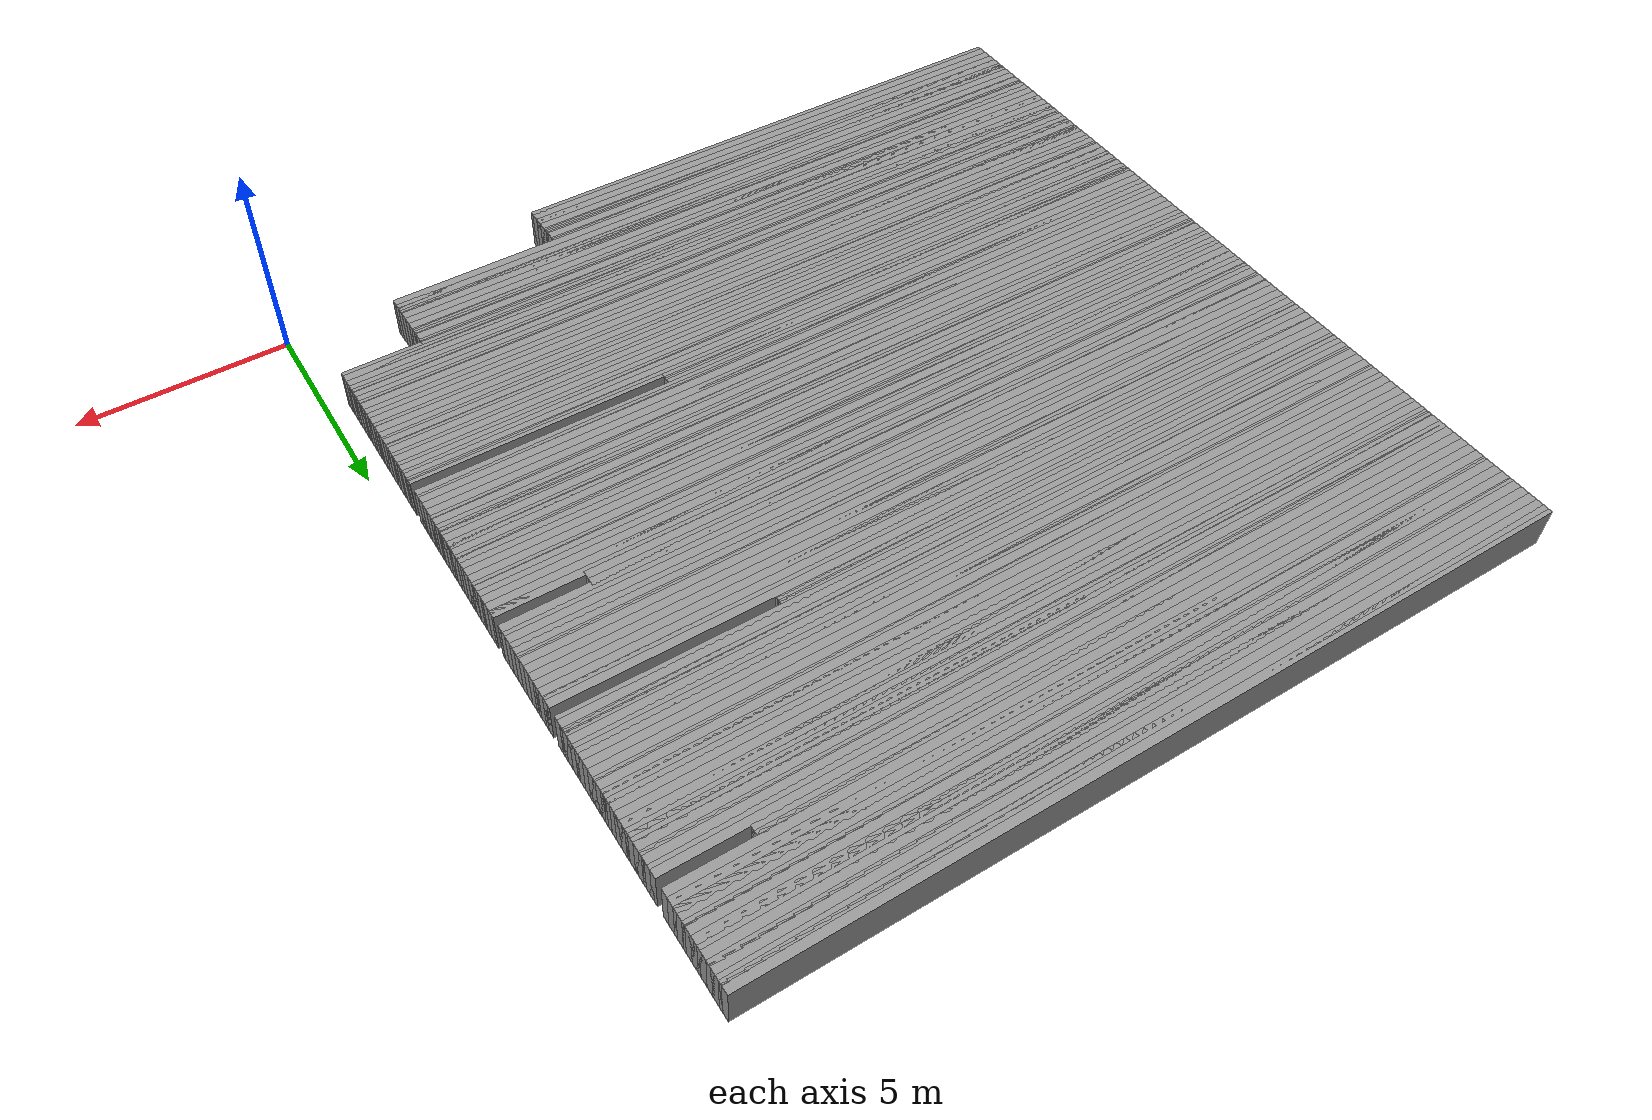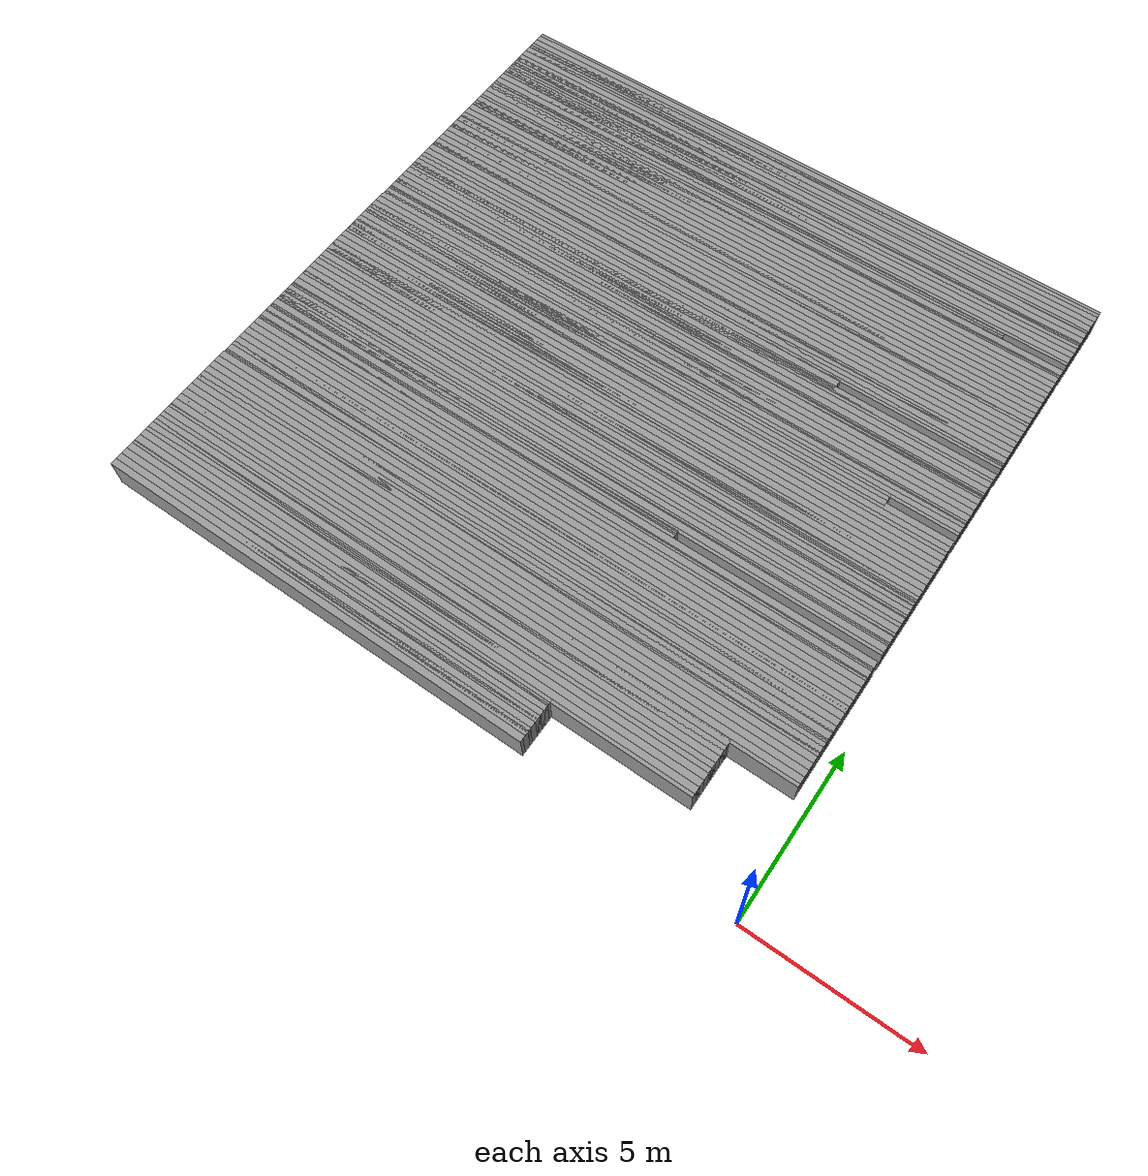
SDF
<?xml version='1.0' encoding='UTF-8'?>
<sdf version="1.6"><world name="GridMap"><model name="GridMap"><pose frame="">0 0 0 0 -0 0</pose><link name="Wall_(131.5,4.0)"><collision name="Wall_(131.5,4.0)_Collision"><geometry><box><size>13.5 0.2 1.0</size></box></geometry><pose frame="">-13.15 0.4 0.5 0 -0 0</pose></collision><visual name="Wall_(131.5,4.0)_Visual"><geometry><box><size>13.5 0.2 1.0</size></box></geometry><pose frame="">-13.15 0.4 0.5 0 -0 0</pose><material><script><uri>file://media/materials/scripts/gazebo.material</uri><name>Gazebo/Grey</name></script><ambient>1 1 1 1</ambient></material><meta><layer>0</layer></meta></visual><pose frame="">0 0 0.5 0 -0 0</pose></link><link name="Wall_(131.5,5.0)"><collision name="Wall_(131.5,5.0)_Collision"><geometry><box><size>13.5 0.2 1.0</size></box></geometry><pose frame="">-13.15 0.5 0.5 0 -0 0</pose></collision><visual name="Wall_(131.5,5.0)_Visual"><geometry><box><size>13.5 0.2 1.0</size></box></geometry><pose frame="">-13.15 0.5 0.5 0 -0 0</pose><material><script><uri>file://media/materials/scripts/gazebo.material</uri><name>Gazebo/Grey</name></script><ambient>1 1 1 1</ambient></material><meta><layer>0</layer></meta></visual><pose frame="">0 0 0.5 0 -0 0</pose></link><link name="Wall_(131.5,6.0)"><collision name="Wall_(131.5,6.0)_Collision"><geometry><box><size>13.5 0.2 1.0</size></box></geometry><pose frame="">-13.15 0.6000000000000001 0.5 0 -0 0</pose></collision><visual name="Wall_(131.5,6.0)_Visual"><geometry><box><size>13.5 0.2 1.0</size></box></geometry><pose frame="">-13.15 0.6000000000000001 0.5 0 -0 0</pose><material><script><uri>file://media/materials/scripts/gazebo.material</uri><name>Gazebo/Grey</name></script><ambient>1 1 1 1</ambient></material><meta><layer>0</layer></meta></visual><pose frame="">0 0 0.5 0 -0 0</pose></link><link name="Wall_(131.5,7.0)"><collision name="Wall_(131.5,7.0)_Collision"><geometry><box><size>13.5 0.2 1.0</size></box></geometry><pose frame="">-13.15 0.7000000000000001 0.5 0 -0 0</pose></collision><visual name="Wall_(131.5,7.0)_Visual"><geometry><box><size>13.5 0.2 1.0</size></box></geometry><pose frame="">-13.15 0.7000000000000001 0.5 0 -0 0</pose><material><script><uri>file://media/materials/scripts/gazebo.material</uri><name>Gazebo/Grey</name></script><ambient>1 1 1 1</ambient></material><meta><layer>0</layer></meta></visual><pose frame="">0 0 0.5 0 -0 0</pose></link><link name="Wall_(131.5,8.0)"><collision name="Wall_(131.5,8.0)_Collision"><geometry><box><size>13.5 0.2 1.0</size></box></geometry><pose frame="">-13.15 0.8 0.5 0 -0 0</pose></collision><visual name="Wall_(131.5,8.0)_Visual"><geometry><box><size>13.5 0.2 1.0</size></box></geometry><pose frame="">-13.15 0.8 0.5 0 -0 0</pose><material><script><uri>file://media/materials/scripts/gazebo.material</uri><name>Gazebo/Grey</name></script><ambient>1 1 1 1</ambient></material><meta><layer>0</layer></meta></visual><pose frame="">0 0 0.5 0 -0 0</pose></link><link name="Wall_(131.5,9.0)"><collision name="Wall_(131.5,9.0)_Collision"><geometry><box><size>13.5 0.2 1.0</size></box></geometry><pose frame="">-13.15 0.9 0.5 0 -0 0</pose></collision><visual name="Wall_(131.5,9.0)_Visual"><geometry><box><size>13.5 0.2 1.0</size></box></geometry><pose frame="">-13.15 0.9 0.5 0 -0 0</pose><material><script><uri>file://media/materials/scripts/gazebo.material</uri><name>Gazebo/Grey</name></script><ambient>1 1 1 1</ambient></material><meta><layer>0</layer></meta></visual><pose frame="">0 0 0.5 0 -0 0</pose></link><link name="Wall_(131.5,10.0)"><collision name="Wall_(131.5,10.0)_Collision"><geometry><box><size>13.5 0.2 1.0</size></box></geometry><pose frame="">-13.15 1.0 0.5 0 -0 0</pose></collision><visual name="Wall_(131.5,10.0)_Visual"><geometry><box><size>13.5 0.2 1.0</size></box></geometry><pose frame="">-13.15 1.0 0.5 0 -0 0</pose><material><script><uri>file://media/materials/scripts/gazebo.material</uri><name>Gazebo/Grey</name></script><ambient>1 1 1 1</ambient></material><meta><layer>0</layer></meta></visual><pose frame="">0 0 0.5 0 -0 0</pose></link><link name="Wall_(131.5,11.0)"><collision name="Wall_(131.5,11.0)_Collision"><geometry><box><size>13.5 0.2 1.0</size></box></geometry><pose frame="">-13.15 1.1 0.5 0 -0 0</pose></collision><visual name="Wall_(131.5,11.0)_Visual"><geometry><box><size>13.5 0.2 1.0</size></box></geometry><pose frame="">-13.15 1.1 0.5 0 -0 0</pose><material><script><uri>file://media/materials/scripts/gazebo.material</uri><name>Gazebo/Grey</name></script><ambient>1 1 1 1</ambient></material><meta><layer>0</layer></meta></visual><pose frame="">0 0 0.5 0 -0 0</pose></link><link name="Wall_(131.5,12.0)"><collision name="Wall_(131.5,12.0)_Collision"><geometry><box><size>13.5 0.2 1.0</size></box></geometry><pose frame="">-13.15 1.2000000000000002 0.5 0 -0 0</pose></collision><visual name="Wall_(131.5,12.0)_Visual"><geometry><box><size>13.5 0.2 1.0</size></box></geometry><pose frame="">-13.15 1.2000000000000002 0.5 0 -0 0</pose><material><script><uri>file://media/materials/scripts/gazebo.material</uri><name>Gazebo/Grey</name></script><ambient>1 1 1 1</ambient></material><meta><layer>0</layer></meta></visual><pose frame="">0 0 0.5 0 -0 0</pose></link><link name="Wall_(131.5,13.0)"><collision name="Wall_(131.5,13.0)_Collision"><geometry><box><size>13.5 0.2 1.0</size></box></geometry><pose frame="">-13.15 1.3 0.5 0 -0 0</pose></collision><visual name="Wall_(131.5,13.0)_Visual"><geometry><box><size>13.5 0.2 1.0</size></box></geometry><pose frame="">-13.15 1.3 0.5 0 -0 0</pose><material><script><uri>file://media/materials/scripts/gazebo.material</uri><name>Gazebo/Grey</name></script><ambient>1 1 1 1</ambient></material><meta><layer>0</layer></meta></visual><pose frame="">0 0 0.5 0 -0 0</pose></link><link name="Wall_(131.5,14.0)"><collision name="Wall_(131.5,14.0)_Collision"><geometry><box><size>13.5 0.2 1.0</size></box></geometry><pose frame="">-13.15 1.4000000000000001 0.5 0 -0 0</pose></collision><visual name="Wall_(131.5,14.0)_Visual"><geometry><box><size>13.5 0.2 1.0</size></box></geometry><pose frame="">-13.15 1.4000000000000001 0.5 0 -0 0</pose><material><script><uri>file://media/materials/scripts/gazebo.material</uri><name>Gazebo/Grey</name></script><ambient>1 1 1 1</ambient></material><meta><layer>0</layer></meta></visual><pose frame="">0 0 0.5 0 -0 0</pose></link><link name="Wall_(131.5,15.0)"><collision name="Wall_(131.5,15.0)_Collision"><geometry><box><size>13.5 0.2 1.0</size></box></geometry><pose frame="">-13.15 1.5 0.5 0 -0 0</pose></collision><visual name="Wall_(131.5,15.0)_Visual"><geometry><box><size>13.5 0.2 1.0</size></box></geometry><pose frame="">-13.15 1.5 0.5 0 -0 0</pose><material><script><uri>file://media/materials/scripts/gazebo.material</uri><name>Gazebo/Grey</name></script><ambient>1 1 1 1</ambient></material><meta><layer>0</layer></meta></visual><pose frame="">0 0 0.5 0 -0 0</pose></link><link name="Wall_(111.0,16.0)"><collision name="Wall_(111.0,16.0)_Collision"><geometry><box><size>17.6 0.2 1.0</size></box></geometry><pose frame="">-11.100000000000001 1.6 0.5 0 -0 0</pose></collision><visual name="Wall_(111.0,16.0)_Visual"><geometry><box><size>17.6 0.2 1.0</size></box></geometry><pose frame="">-11.100000000000001 1.6 0.5 0 -0 0</pose><material><script><uri>file://media/materials/scripts/gazebo.material</uri><name>Gazebo/Grey</name></script><ambient>1 1 1 1</ambient></material><meta><layer>0</layer></meta></visual><pose frame="">0 0 0.5 0 -0 0</pose></link><link name="Wall_(111.0,17.0)"><collision name="Wall_(111.0,17.0)_Collision"><geometry><box><size>17.6 0.2 1.0</size></box></geometry><pose frame="">-11.100000000000001 1.7000000000000002 0.5 0 -0 0</pose></collision><visual name="Wall_(111.0,17.0)_Visual"><geometry><box><size>17.6 0.2 1.0</size></box></geometry><pose frame="">-11.100000000000001 1.7000000000000002 0.5 0 -0 0</pose><material><script><uri>file://media/materials/scripts/gazebo.material</uri><name>Gazebo/Grey</name></script><ambient>1 1 1 1</ambient></material><meta><layer>0</layer></meta></visual><pose frame="">0 0 0.5 0 -0 0</pose></link><link name="Wall_(111.0,18.0)"><collision name="Wall_(111.0,18.0)_Collision"><geometry><box><size>17.6 0.2 1.0</size></box></geometry><pose frame="">-11.100000000000001 1.8 0.5 0 -0 0</pose></collision><visual name="Wall_(111.0,18.0)_Visual"><geometry><box><size>17.6 0.2 1.0</size></box></geometry><pose frame="">-11.100000000000001 1.8 0.5 0 -0 0</pose><material><script><uri>file://media/materials/scripts/gazebo.material</uri><name>Gazebo/Grey</name></script><ambient>1 1 1 1</ambient></material><meta><layer>0</layer></meta></visual><pose frame="">0 0 0.5 0 -0 0</pose></link><link name="Wall_(111.0,19.0)"><collision name="Wall_(111.0,19.0)_Collision"><geometry><box><size>17.6 0.2 1.0</size></box></geometry><pose frame="">-11.100000000000001 1.9000000000000001 0.5 0 -0 0</pose></collision><visual name="Wall_(111.0,19.0)_Visual"><geometry><box><size>17.6 0.2 1.0</size></box></geometry><pose frame="">-11.100000000000001 1.9000000000000001 0.5 0 -0 0</pose><material><script><uri>file://media/materials/scripts/gazebo.material</uri><name>Gazebo/Grey</name></script><ambient>1 1 1 1</ambient></material><meta><layer>0</layer></meta></visual><pose frame="">0 0 0.5 0 -0 0</pose></link><link name="Wall_(111.0,20.0)"><collision name="Wall_(111.0,20.0)_Collision"><geometry><box><size>17.6 0.2 1.0</size></box></geometry><pose frame="">-11.100000000000001 2.0 0.5 0 -0 0</pose></collision><visual name="Wall_(111.0,20.0)_Visual"><geometry><box><size>17.6 0.2 1.0</size></box></geometry><pose frame="">-11.100000000000001 2.0 0.5 0 -0 0</pose><material><script><uri>file://media/materials/scripts/gazebo.material</uri><name>Gazebo/Grey</name></script><ambient>1 1 1 1</ambient></material><meta><layer>0</layer></meta></visual><pose frame="">0 0 0.5 0 -0 0</pose></link><link name="Wall_(111.0,21.0)"><collision name="Wall_(111.0,21.0)_Collision"><geometry><box><size>17.6 0.2 1.0</size></box></geometry><pose frame="">-11.100000000000001 2.1 0.5 0 -0 0</pose></collision><visual name="Wall_(111.0,21.0)_Visual"><geometry><box><size>17.6 0.2 1.0</size></box></geometry><pose frame="">-11.100000000000001 2.1 0.5 0 -0 0</pose><material><script><uri>file://media/materials/scripts/gazebo.material</uri><name>Gazebo/Grey</name></script><ambient>1 1 1 1</ambient></material><meta><layer>0</layer></meta></visual><pose frame="">0 0 0.5 0 -0 0</pose></link><link name="Wall_(111.0,22.0)"><collision name="Wall_(111.0,22.0)_Collision"><geometry><box><size>17.6 0.2 1.0</size></box></geometry><pose frame="">-11.100000000000001 2.2 0.5 0 -0 0</pose></collision><visual name="Wall_(111.0,22.0)_Visual"><geometry><box><size>17.6 0.2 1.0</size></box></geometry><pose frame="">-11.100000000000001 2.2 0.5 0 -0 0</pose><material><script><uri>file://media/materials/scripts/gazebo.material</uri><name>Gazebo/Grey</name></script><ambient>1 1 1 1</ambient></material><meta><layer>0</layer></meta></visual><pose frame="">0 0 0.5 0 -0 0</pose></link><link name="Wall_(111.0,23.0)"><collision name="Wall_(111.0,23.0)_Collision"><geometry><box><size>17.6 0.2 1.0</size></box></geometry><pose frame="">-11.100000000000001 2.3000000000000003 0.5 0 -0 0</pose></collision><visual name="Wall_(111.0,23.0)_Visual"><geometry><box><size>17.6 0.2 1.0</size></box></geometry><pose frame="">-11.100000000000001 2.3000000000000003 0.5 0 -0 0</pose><material><script><uri>file://media/materials/scripts/gazebo.material</uri><name>Gazebo/Grey</name></script><ambient>1 1 1 1</ambient></material><meta><layer>0</layer></meta></visual><pose frame="">0 0 0.5 0 -0 0</pose></link><link name="Wall_(111.0,24.0)"><collision name="Wall_(111.0,24.0)_Collision"><geometry><box><size>17.6 0.2 1.0</size></box></geometry><pose frame="">-11.100000000000001 2.4000000000000004 0.5 0 -0 0</pose></collision><visual name="Wall_(111.0,24.0)_Visual"><geometry><box><size>17.6 0.2 1.0</size></box></geometry><pose frame="">-11.100000000000001 2.4000000000000004 0.5 0 -0 0</pose><material><script><uri>file://media/materials/scripts/gazebo.material</uri><name>Gazebo/Grey</name></script><ambient>1 1 1 1</ambient></material><meta><layer>0</layer></meta></visual><pose frame="">0 0 0.5 0 -0 0</pose></link><link name="Wall_(111.0,25.0)"><collision name="Wall_(111.0,25.0)_Collision"><geometry><box><size>17.6 0.2 1.0</size></box></geometry><pose frame="">-11.100000000000001 2.5 0.5 0 -0 0</pose></collision><visual name="Wall_(111.0,25.0)_Visual"><geometry><box><size>17.6 0.2 1.0</size></box></geometry><pose frame="">-11.100000000000001 2.5 0.5 0 -0 0</pose><material><script><uri>file://media/materials/scripts/gazebo.material</uri><name>Gazebo/Grey</name></script><ambient>1 1 1 1</ambient></material><meta><layer>0</layer></meta></visual><pose frame="">0 0 0.5 0 -0 0</pose></link><link name="Wall_(111.0,26.0)"><collision name="Wall_(111.0,26.0)_Collision"><geometry><box><size>17.6 0.2 1.0</size></box></geometry><pose frame="">-11.100000000000001 2.6 0.5 0 -0 0</pose></collision><visual name="Wall_(111.0,26.0)_Visual"><geometry><box><size>17.6 0.2 1.0</size></box></geometry><pose frame="">-11.100000000000001 2.6 0.5 0 -0 0</pose><material><script><uri>file://media/materials/scripts/gazebo.material</uri><name>Gazebo/Grey</name></script><ambient>1 1 1 1</ambient></material><meta><layer>0</layer></meta></visual><pose frame="">0 0 0.5 0 -0 0</pose></link><link name="Wall_(111.0,27.0)"><collision name="Wall_(111.0,27.0)_Collision"><geometry><box><size>17.6 0.2 1.0</size></box></geometry><pose frame="">-11.100000000000001 2.7 0.5 0 -0 0</pose></collision><visual name="Wall_(111.0,27.0)_Visual"><geometry><box><size>17.6 0.2 1.0</size></box></geometry><pose frame="">-11.100000000000001 2.7 0.5 0 -0 0</pose><material><script><uri>file://media/materials/scripts/gazebo.material</uri><name>Gazebo/Grey</name></script><ambient>1 1 1 1</ambient></material><meta><layer>0</layer></meta></visual><pose frame="">0 0 0.5 0 -0 0</pose></link><link name="Wall_(111.0,28.0)"><collision name="Wall_(111.0,28.0)_Collision"><geometry><box><size>17.6 0.2 1.0</size></box></geometry><pose frame="">-11.100000000000001 2.8000000000000003 0.5 0 -0 0</pose></collision><visual name="Wall_(111.0,28.0)_Visual"><geometry><box><size>17.6 0.2 1.0</size></box></geometry><pose frame="">-11.100000000000001 2.8000000000000003 0.5 0 -0 0</pose><material><script><uri>file://media/materials/scripts/gazebo.material</uri><name>Gazebo/Grey</name></script><ambient>1 1 1 1</ambient></material><meta><layer>0</layer></meta></visual><pose frame="">0 0 0.5 0 -0 0</pose></link><link name="Wall_(111.0,29.0)"><collision name="Wall_(111.0,29.0)_Collision"><geometry><box><size>17.6 0.2 1.0</size></box></geometry><pose frame="">-11.100000000000001 2.9000000000000004 0.5 0 -0 0</pose></collision><visual name="Wall_(111.0,29.0)_Visual"><geometry><box><size>17.6 0.2 1.0</size></box></geometry><pose frame="">-11.100000000000001 2.9000000000000004 0.5 0 -0 0</pose><material><script><uri>file://media/materials/scripts/gazebo.material</uri><name>Gazebo/Grey</name></script><ambient>1 1 1 1</ambient></material><meta><layer>0</layer></meta></visual><pose frame="">0 0 0.5 0 -0 0</pose></link><link name="Wall_(111.0,30.0)"><collision name="Wall_(111.0,30.0)_Collision"><geometry><box><size>17.6 0.2 1.0</size></box></geometry><pose frame="">-11.100000000000001 3.0 0.5 0 -0 0</pose></collision><visual name="Wall_(111.0,30.0)_Visual"><geometry><box><size>17.6 0.2 1.0</size></box></geometry><pose frame="">-11.100000000000001 3.0 0.5 0 -0 0</pose><material><script><uri>file://media/materials/scripts/gazebo.material</uri><name>Gazebo/Grey</name></script><ambient>1 1 1 1</ambient></material><meta><layer>0</layer></meta></visual><pose frame="">0 0 0.5 0 -0 0</pose></link><link name="Wall_(111.0,31.0)"><collision name="Wall_(111.0,31.0)_Collision"><geometry><box><size>17.6 0.2 1.0</size></box></geometry><pose frame="">-11.100000000000001 3.1 0.5 0 -0 0</pose></collision><visual name="Wall_(111.0,31.0)_Visual"><geometry><box><size>17.6 0.2 1.0</size></box></geometry><pose frame="">-11.100000000000001 3.1 0.5 0 -0 0</pose><material><script><uri>file://media/materials/scripts/gazebo.material</uri><name>Gazebo/Grey</name></script><ambient>1 1 1 1</ambient></material><meta><layer>0</layer></meta></visual><pose frame="">0 0 0.5 0 -0 0</pose></link><link name="Wall_(101.5,32.0)"><collision name="Wall_(101.5,32.0)_Collision"><geometry><box><size>19.5 0.2 1.0</size></box></geometry><pose frame="">-10.15 3.2 0.5 0 -0 0</pose></collision><visual name="Wall_(101.5,32.0)_Visual"><geometry><box><size>19.5 0.2 1.0</size></box></geometry><pose frame="">-10.15 3.2 0.5 0 -0 0</pose><material><script><uri>file://media/materials/scripts/gazebo.material</uri><name>Gazebo/Grey</name></script><ambient>1 1 1 1</ambient></material><meta><layer>0</layer></meta></visual><pose frame="">0 0 0.5 0 -0 0</pose></link><link name="Wall_(101.5,33.0)"><collision name="Wall_(101.5,33.0)_Collision"><geometry><box><size>19.5 0.2 1.0</size></box></geometry><pose frame="">-10.15 3.3000000000000003 0.5 0 -0 0</pose></collision><visual name="Wall_(101.5,33.0)_Visual"><geometry><box><size>19.5 0.2 1.0</size></box></geometry><pose frame="">-10.15 3.3000000000000003 0.5 0 -0 0</pose><material><script><uri>file://media/materials/scripts/gazebo.material</uri><name>Gazebo/Grey</name></script><ambient>1 1 1 1</ambient></material><meta><layer>0</layer></meta></visual><pose frame="">0 0 0.5 0 -0 0</pose></link><link name="Wall_(101.5,34.0)"><collision name="Wall_(101.5,34.0)_Collision"><geometry><box><size>19.5 0.2 1.0</size></box></geometry><pose frame="">-10.15 3.4000000000000004 0.5 0 -0 0</pose></collision><visual name="Wall_(101.5,34.0)_Visual"><geometry><box><size>19.5 0.2 1.0</size></box></geometry><pose frame="">-10.15 3.4000000000000004 0.5 0 -0 0</pose><material><script><uri>file://media/materials/scripts/gazebo.material</uri><name>Gazebo/Grey</name></script><ambient>1 1 1 1</ambient></material><meta><layer>0</layer></meta></visual><pose frame="">0 0 0.5 0 -0 0</pose></link><link name="Wall_(101.5,35.0)"><collision name="Wall_(101.5,35.0)_Collision"><geometry><box><size>19.5 0.2 1.0</size></box></geometry><pose frame="">-10.15 3.5 0.5 0 -0 0</pose></collision><visual name="Wall_(101.5,35.0)_Visual"><geometry><box><size>19.5 0.2 1.0</size></box></geometry><pose frame="">-10.15 3.5 0.5 0 -0 0</pose><material><script><uri>file://media/materials/scripts/gazebo.material</uri><name>Gazebo/Grey</name></script><ambient>1 1 1 1</ambient></material><meta><layer>0</layer></meta></visual><pose frame="">0 0 0.5 0 -0 0</pose></link><link name="Wall_(101.5,36.0)"><collision name="Wall_(101.5,36.0)_Collision"><geometry><box><size>19.5 0.2 1.0</size></box></geometry><pose frame="">-10.15 3.6 0.5 0 -0 0</pose></collision><visual name="Wall_(101.5,36.0)_Visual"><geometry><box><size>19.5 0.2 1.0</size></box></geometry><pose frame="">-10.15 3.6 0.5 0 -0 0</pose><material><script><uri>file://media/materials/scripts/gazebo.material</uri><name>Gazebo/Grey</name></script><ambient>1 1 1 1</ambient></material><meta><layer>0</layer></meta></visual><pose frame="">0 0 0.5 0 -0 0</pose></link><link name="Wall_(101.5,37.0)"><collision name="Wall_(101.5,37.0)_Collision"><geometry><box><size>19.5 0.2 1.0</size></box></geometry><pose frame="">-10.15 3.7 0.5 0 -0 0</pose></collision><visual name="Wall_(101.5,37.0)_Visual"><geometry><box><size>19.5 0.2 1.0</size></box></geometry><pose frame="">-10.15 3.7 0.5 0 -0 0</pose><material><script><uri>file://media/materials/scripts/gazebo.material</uri><name>Gazebo/Grey</name></script><ambient>1 1 1 1</ambient></material><meta><layer>0</layer></meta></visual><pose frame="">0 0 0.5 0 -0 0</pose></link><link name="Wall_(101.5,38.0)"><collision name="Wall_(101.5,38.0)_Collision"><geometry><box><size>19.5 0.2 1.0</size></box></geometry><pose frame="">-10.15 3.8000000000000003 0.5 0 -0 0</pose></collision><visual name="Wall_(101.5,38.0)_Visual"><geometry><box><size>19.5 0.2 1.0</size></box></geometry><pose frame="">-10.15 3.8000000000000003 0.5 0 -0 0</pose><material><script><uri>file://media/materials/scripts/gazebo.material</uri><name>Gazebo/Grey</name></script><ambient>1 1 1 1</ambient></material><meta><layer>0</layer></meta></visual><pose frame="">0 0 0.5 0 -0 0</pose></link><link name="Wall_(101.5,39.0)"><collision name="Wall_(101.5,39.0)_Collision"><geometry><box><size>19.5 0.2 1.0</size></box></geometry><pose frame="">-10.15 3.9000000000000004 0.5 0 -0 0</pose></collision><visual name="Wall_(101.5,39.0)_Visual"><geometry><box><size>19.5 0.2 1.0</size></box></geometry><pose frame="">-10.15 3.9000000000000004 0.5 0 -0 0</pose><material><script><uri>file://media/materials/scripts/gazebo.material</uri><name>Gazebo/Grey</name></script><ambient>1 1 1 1</ambient></material><meta><layer>0</layer></meta></visual><pose frame="">0 0 0.5 0 -0 0</pose></link><link name="Wall_(101.5,40.0)"><collision name="Wall_(101.5,40.0)_Collision"><geometry><box><size>19.5 0.2 1.0</size></box></geometry><pose frame="">-10.15 4.0 0.5 0 -0 0</pose></collision><visual name="Wall_(101.5,40.0)_Visual"><geometry><box><size>19.5 0.2 1.0</size></box></geometry><pose frame="">-10.15 4.0 0.5 0 -0 0</pose><material><script><uri>file://media/materials/scripts/gazebo.material</uri><name>Gazebo/Grey</name></script><ambient>1 1 1 1</ambient></material><meta><layer>0</layer></meta></visual><pose frame="">0 0 0.5 0 -0 0</pose></link><link name="Wall_(101.5,41.0)"><collision name="Wall_(101.5,41.0)_Collision"><geometry><box><size>19.5 0.2 1.0</size></box></geometry><pose frame="">-10.15 4.1000000000000005 0.5 0 -0 0</pose></collision><visual name="Wall_(101.5,41.0)_Visual"><geometry><box><size>19.5 0.2 1.0</size></box></geometry><pose frame="">-10.15 4.1000000000000005 0.5 0 -0 0</pose><material><script><uri>file://media/materials/scripts/gazebo.material</uri><name>Gazebo/Grey</name></script><ambient>1 1 1 1</ambient></material><meta><layer>0</layer></meta></visual><pose frame="">0 0 0.5 0 -0 0</pose></link><link name="Wall_(101.5,42.0)"><collision name="Wall_(101.5,42.0)_Collision"><geometry><box><size>19.5 0.2 1.0</size></box></geometry><pose frame="">-10.15 4.2 0.5 0 -0 0</pose></collision><visual name="Wall_(101.5,42.0)_Visual"><geometry><box><size>19.5 0.2 1.0</size></box></geometry><pose frame="">-10.15 4.2 0.5 0 -0 0</pose><material><script><uri>file://media/materials/scripts/gazebo.material</uri><name>Gazebo/Grey</name></script><ambient>1 1 1 1</ambient></material><meta><layer>0</layer></meta></visual><pose frame="">0 0 0.5 0 -0 0</pose></link><link name="Wall_(101.5,43.0)"><collision name="Wall_(101.5,43.0)_Collision"><geometry><box><size>19.5 0.2 1.0</size></box></geometry><pose frame="">-10.15 4.3 0.5 0 -0 0</pose></collision><visual name="Wall_(101.5,43.0)_Visual"><geometry><box><size>19.5 0.2 1.0</size></box></geometry><pose frame="">-10.15 4.3 0.5 0 -0 0</pose><material><script><uri>file://media/materials/scripts/gazebo.material</uri><name>Gazebo/Grey</name></script><ambient>1 1 1 1</ambient></material><meta><layer>0</layer></meta></visual><pose frame="">0 0 0.5 0 -0 0</pose></link><link name="Wall_(101.5,44.0)"><collision name="Wall_(101.5,44.0)_Collision"><geometry><box><size>19.5 0.2 1.0</size></box></geometry><pose frame="">-10.15 4.4 0.5 0 -0 0</pose></collision><visual name="Wall_(101.5,44.0)_Visual"><geometry><box><size>19.5 0.2 1.0</size></box></geometry><pose frame="">-10.15 4.4 0.5 0 -0 0</pose><material><script><uri>file://media/materials/scripts/gazebo.material</uri><name>Gazebo/Grey</name></script><ambient>1 1 1 1</ambient></material><meta><layer>0</layer></meta></visual><pose frame="">0 0 0.5 0 -0 0</pose></link><link name="Wall_(101.5,45.0)"><collision name="Wall_(101.5,45.0)_Collision"><geometry><box><size>19.5 0.2 1.0</size></box></geometry><pose frame="">-10.15 4.5 0.5 0 -0 0</pose></collision><visual name="Wall_(101.5,45.0)_Visual"><geometry><box><size>19.5 0.2 1.0</size></box></geometry><pose frame="">-10.15 4.5 0.5 0 -0 0</pose><material><script><uri>file://media/materials/scripts/gazebo.material</uri><name>Gazebo/Grey</name></script><ambient>1 1 1 1</ambient></material><meta><layer>0</layer></meta></visual><pose frame="">0 0 0.5 0 -0 0</pose></link><link name="Wall_(101.5,46.0)"><collision name="Wall_(101.5,46.0)_Collision"><geometry><box><size>19.5 0.2 1.0</size></box></geometry><pose frame="">-10.15 4.6000000000000005 0.5 0 -0 0</pose></collision><visual name="Wall_(101.5,46.0)_Visual"><geometry><box><size>19.5 0.2 1.0</size></box></geometry><pose frame="">-10.15 4.6000000000000005 0.5 0 -0 0</pose><material><script><uri>file://media/materials/scripts/gazebo.material</uri><name>Gazebo/Grey</name></script><ambient>1 1 1 1</ambient></material><meta><layer>0</layer></meta></visual><pose frame="">0 0 0.5 0 -0 0</pose></link><link name="Wall_(101.5,47.0)"><collision name="Wall_(101.5,47.0)_Collision"><geometry><box><size>19.5 0.2 1.0</size></box></geometry><pose frame="">-10.15 4.7 0.5 0 -0 0</pose></collision><visual name="Wall_(101.5,47.0)_Visual"><geometry><box><size>19.5 0.2 1.0</size></box></geometry><pose frame="">-10.15 4.7 0.5 0 -0 0</pose><material><script><uri>file://media/materials/scripts/gazebo.material</uri><name>Gazebo/Grey</name></script><ambient>1 1 1 1</ambient></material><meta><layer>0</layer></meta></visual><pose frame="">0 0 0.5 0 -0 0</pose></link><link name="Wall_(101.5,48.0)"><collision name="Wall_(101.5,48.0)_Collision"><geometry><box><size>19.5 0.2 1.0</size></box></geometry><pose frame="">-10.15 4.800000000000001 0.5 0 -0 0</pose></collision><visual name="Wall_(101.5,48.0)_Visual"><geometry><box><size>19.5 0.2 1.0</size></box></geometry><pose frame="">-10.15 4.800000000000001 0.5 0 -0 0</pose><material><script><uri>file://media/materials/scripts/gazebo.material</uri><name>Gazebo/Grey</name></script><ambient>1 1 1 1</ambient></material><meta><layer>0</layer></meta></visual><pose frame="">0 0 0.5 0 -0 0</pose></link><link name="Wall_(101.5,49.0)"><collision name="Wall_(101.5,49.0)_Collision"><geometry><box><size>19.5 0.2 1.0</size></box></geometry><pose frame="">-10.15 4.9 0.5 0 -0 0</pose></collision><visual name="Wall_(101.5,49.0)_Visual"><geometry><box><size>19.5 0.2 1.0</size></box></geometry><pose frame="">-10.15 4.9 0.5 0 -0 0</pose><material><script><uri>file://media/materials/scripts/gazebo.material</uri><name>Gazebo/Grey</name></script><ambient>1 1 1 1</ambient></material><meta><layer>0</layer></meta></visual><pose frame="">0 0 0.5 0 -0 0</pose></link><link name="Wall_(101.5,50.0)"><collision name="Wall_(101.5,50.0)_Collision"><geometry><box><size>19.5 0.2 1.0</size></box></geometry><pose frame="">-10.15 5.0 0.5 0 -0 0</pose></collision><visual name="Wall_(101.5,50.0)_Visual"><geometry><box><size>19.5 0.2 1.0</size></box></geometry><pose frame="">-10.15 5.0 0.5 0 -0 0</pose><material><script><uri>file://media/materials/scripts/gazebo.material</uri><name>Gazebo/Grey</name></script><ambient>1 1 1 1</ambient></material><meta><layer>0</layer></meta></visual><pose frame="">0 0 0.5 0 -0 0</pose></link><link name="Wall_(101.5,51.0)"><collision name="Wall_(101.5,51.0)_Collision"><geometry><box><size>19.5 0.2 1.0</size></box></geometry><pose frame="">-10.15 5.1000000000000005 0.5 0 -0 0</pose></collision><visual name="Wall_(101.5,51.0)_Visual"><geometry><box><size>19.5 0.2 1.0</size></box></geometry><pose frame="">-10.15 5.1000000000000005 0.5 0 -0 0</pose><material><script><uri>file://media/materials/scripts/gazebo.material</uri><name>Gazebo/Grey</name></script><ambient>1 1 1 1</ambient></material><meta><layer>0</layer></meta></visual><pose frame="">0 0 0.5 0 -0 0</pose></link><link name="Wall_(101.5,52.0)"><collision name="Wall_(101.5,52.0)_Collision"><geometry><box><size>19.5 0.2 1.0</size></box></geometry><pose frame="">-10.15 5.2 0.5 0 -0 0</pose></collision><visual name="Wall_(101.5,52.0)_Visual"><geometry><box><size>19.5 0.2 1.0</size></box></geometry><pose frame="">-10.15 5.2 0.5 0 -0 0</pose><material><script><uri>file://media/materials/scripts/gazebo.material</uri><name>Gazebo/Grey</name></script><ambient>1 1 1 1</ambient></material><meta><layer>0</layer></meta></visual><pose frame="">0 0 0.5 0 -0 0</pose></link><link name="Wall_(101.5,53.0)"><collision name="Wall_(101.5,53.0)_Collision"><geometry><box><size>19.5 0.2 1.0</size></box></geometry><pose frame="">-10.15 5.300000000000001 0.5 0 -0 0</pose></collision><visual name="Wall_(101.5,53.0)_Visual"><geometry><box><size>19.5 0.2 1.0</size></box></geometry><pose frame="">-10.15 5.300000000000001 0.5 0 -0 0</pose><material><script><uri>file://media/materials/scripts/gazebo.material</uri><name>Gazebo/Grey</name></script><ambient>1 1 1 1</ambient></material><meta><layer>0</layer></meta></visual><pose frame="">0 0 0.5 0 -0 0</pose></link><link name="Wall_(101.5,54.0)"><collision name="Wall_(101.5,54.0)_Collision"><geometry><box><size>19.5 0.2 1.0</size></box></geometry><pose frame="">-10.15 5.4 0.5 0 -0 0</pose></collision><visual name="Wall_(101.5,54.0)_Visual"><geometry><box><size>19.5 0.2 1.0</size></box></geometry><pose frame="">-10.15 5.4 0.5 0 -0 0</pose><material><script><uri>file://media/materials/scripts/gazebo.material</uri><name>Gazebo/Grey</name></script><ambient>1 1 1 1</ambient></material><meta><layer>0</layer></meta></visual><pose frame="">0 0 0.5 0 -0 0</pose></link><link name="Wall_(101.5,55.0)"><collision name="Wall_(101.5,55.0)_Collision"><geometry><box><size>19.5 0.2 1.0</size></box></geometry><pose frame="">-10.15 5.5 0.5 0 -0 0</pose></collision><visual name="Wall_(101.5,55.0)_Visual"><geometry><box><size>19.5 0.2 1.0</size></box></geometry><pose frame="">-10.15 5.5 0.5 0 -0 0</pose><material><script><uri>file://media/materials/scripts/gazebo.material</uri><name>Gazebo/Grey</name></script><ambient>1 1 1 1</ambient></material><meta><layer>0</layer></meta></visual><pose frame="">0 0 0.5 0 -0 0</pose></link><link name="Wall_(101.5,56.0)"><collision name="Wall_(101.5,56.0)_Collision"><geometry><box><size>19.5 0.2 1.0</size></box></geometry><pose frame="">-10.15 5.6000000000000005 0.5 0 -0 0</pose></collision><visual name="Wall_(101.5,56.0)_Visual"><geometry><box><size>19.5 0.2 1.0</size></box></geometry><pose frame="">-10.15 5.6000000000000005 0.5 0 -0 0</pose><material><script><uri>file://media/materials/scripts/gazebo.material</uri><name>Gazebo/Grey</name></script><ambient>1 1 1 1</ambient></material><meta><layer>0</layer></meta></visual><pose frame="">0 0 0.5 0 -0 0</pose></link><link name="Wall_(101.5,57.0)"><collision name="Wall_(101.5,57.0)_Collision"><geometry><box><size>19.5 0.2 1.0</size></box></geometry><pose frame="">-10.15 5.7 0.5 0 -0 0</pose></collision><visual name="Wall_(101.5,57.0)_Visual"><geometry><box><size>19.5 0.2 1.0</size></box></geometry><pose frame="">-10.15 5.7 0.5 0 -0 0</pose><material><script><uri>file://media/materials/scripts/gazebo.material</uri><name>Gazebo/Grey</name></script><ambient>1 1 1 1</ambient></material><meta><layer>0</layer></meta></visual><pose frame="">0 0 0.5 0 -0 0</pose></link><link name="Wall_(101.5,58.0)"><collision name="Wall_(101.5,58.0)_Collision"><geometry><box><size>19.5 0.2 1.0</size></box></geometry><pose frame="">-10.15 5.800000000000001 0.5 0 -0 0</pose></collision><visual name="Wall_(101.5,58.0)_Visual"><geometry><box><size>19.5 0.2 1.0</size></box></geometry><pose frame="">-10.15 5.800000000000001 0.5 0 -0 0</pose><material><script><uri>file://media/materials/scripts/gazebo.material</uri><name>Gazebo/Grey</name></script><ambient>1 1 1 1</ambient></material><meta><layer>0</layer></meta></visual><pose frame="">0 0 0.5 0 -0 0</pose></link><link name="Wall_(101.5,59.0)"><collision name="Wall_(101.5,59.0)_Collision"><geometry><box><size>19.5 0.2 1.0</size></box></geometry><pose frame="">-10.15 5.9 0.5 0 -0 0</pose></collision><visual name="Wall_(101.5,59.0)_Visual"><geometry><box><size>19.5 0.2 1.0</size></box></geometry><pose frame="">-10.15 5.9 0.5 0 -0 0</pose><material><script><uri>file://media/materials/scripts/gazebo.material</uri><name>Gazebo/Grey</name></script><ambient>1 1 1 1</ambient></material><meta><layer>0</layer></meta></visual><pose frame="">0 0 0.5 0 -0 0</pose></link><link name="Wall_(101.5,60.0)"><collision name="Wall_(101.5,60.0)_Collision"><geometry><box><size>19.5 0.2 1.0</size></box></geometry><pose frame="">-10.15 6.0 0.5 0 -0 0</pose></collision><visual name="Wall_(101.5,60.0)_Visual"><geometry><box><size>19.5 0.2 1.0</size></box></geometry><pose frame="">-10.15 6.0 0.5 0 -0 0</pose><material><script><uri>file://media/materials/scripts/gazebo.material</uri><name>Gazebo/Grey</name></script><ambient>1 1 1 1</ambient></material><meta><layer>0</layer></meta></visual><pose frame="">0 0 0.5 0 -0 0</pose></link><link name="Wall_(101.5,61.0)"><collision name="Wall_(101.5,61.0)_Collision"><geometry><box><size>19.5 0.2 1.0</size></box></geometry><pose frame="">-10.15 6.1000000000000005 0.5 0 -0 0</pose></collision><visual name="Wall_(101.5,61.0)_Visual"><geometry><box><size>19.5 0.2 1.0</size></box></geometry><pose frame="">-10.15 6.1000000000000005 0.5 0 -0 0</pose><material><script><uri>file://media/materials/scripts/gazebo.material</uri><name>Gazebo/Grey</name></script><ambient>1 1 1 1</ambient></material><meta><layer>0</layer></meta></visual><pose frame="">0 0 0.5 0 -0 0</pose></link><link name="Wall_(101.5,62.0)"><collision name="Wall_(101.5,62.0)_Collision"><geometry><box><size>19.5 0.2 1.0</size></box></geometry><pose frame="">-10.15 6.2 0.5 0 -0 0</pose></collision><visual name="Wall_(101.5,62.0)_Visual"><geometry><box><size>19.5 0.2 1.0</size></box></geometry><pose frame="">-10.15 6.2 0.5 0 -0 0</pose><material><script><uri>file://media/materials/scripts/gazebo.material</uri><name>Gazebo/Grey</name></script><ambient>1 1 1 1</ambient></material><meta><layer>0</layer></meta></visual><pose frame="">0 0 0.5 0 -0 0</pose></link><link name="Wall_(101.5,63.0)"><collision name="Wall_(101.5,63.0)_Collision"><geometry><box><size>19.5 0.2 1.0</size></box></geometry><pose frame="">-10.15 6.300000000000001 0.5 0 -0 0</pose></collision><visual name="Wall_(101.5,63.0)_Visual"><geometry><box><size>19.5 0.2 1.0</size></box></geometry><pose frame="">-10.15 6.300000000000001 0.5 0 -0 0</pose><material><script><uri>file://media/materials/scripts/gazebo.material</uri><name>Gazebo/Grey</name></script><ambient>1 1 1 1</ambient></material><meta><layer>0</layer></meta></visual><pose frame="">0 0 0.5 0 -0 0</pose></link><link name="Wall_(101.5,64.0)"><collision name="Wall_(101.5,64.0)_Collision"><geometry><box><size>19.5 0.2 1.0</size></box></geometry><pose frame="">-10.15 6.4 0.5 0 -0 0</pose></collision><visual name="Wall_(101.5,64.0)_Visual"><geometry><box><size>19.5 0.2 1.0</size></box></geometry><pose frame="">-10.15 6.4 0.5 0 -0 0</pose><material><script><uri>file://media/materials/scripts/gazebo.material</uri><name>Gazebo/Grey</name></script><ambient>1 1 1 1</ambient></material><meta><layer>0</layer></meta></visual><pose frame="">0 0 0.5 0 -0 0</pose></link><link name="Wall_(101.5,65.0)"><collision name="Wall_(101.5,65.0)_Collision"><geometry><box><size>19.5 0.2 1.0</size></box></geometry><pose frame="">-10.15 6.5 0.5 0 -0 0</pose></collision><visual name="Wall_(101.5,65.0)_Visual"><geometry><box><size>19.5 0.2 1.0</size></box></geometry><pose frame="">-10.15 6.5 0.5 0 -0 0</pose><material><script><uri>file://media/materials/scripts/gazebo.material</uri><name>Gazebo/Grey</name></script><ambient>1 1 1 1</ambient></material><meta><layer>0</layer></meta></visual><pose frame="">0 0 0.5 0 -0 0</pose></link><link name="Wall_(101.5,66.0)"><collision name="Wall_(101.5,66.0)_Collision"><geometry><box><size>19.5 0.2 1.0</size></box></geometry><pose frame="">-10.15 6.6000000000000005 0.5 0 -0 0</pose></collision><visual name="Wall_(101.5,66.0)_Visual"><geometry><box><size>19.5 0.2 1.0</size></box></geometry><pose frame="">-10.15 6.6000000000000005 0.5 0 -0 0</pose><material><script><uri>file://media/materials/scripts/gazebo.material</uri><name>Gazebo/Grey</name></script><ambient>1 1 1 1</ambient></material><meta><layer>0</layer></meta></visual><pose frame="">0 0 0.5 0 -0 0</pose></link><link name="Wall_(101.5,67.0)"><collision name="Wall_(101.5,67.0)_Collision"><geometry><box><size>19.5 0.2 1.0</size></box></geometry><pose frame="">-10.15 6.7 0.5 0 -0 0</pose></collision><visual name="Wall_(101.5,67.0)_Visual"><geometry><box><size>19.5 0.2 1.0</size></box></geometry><pose frame="">-10.15 6.7 0.5 0 -0 0</pose><material><script><uri>file://media/materials/scripts/gazebo.material</uri><name>Gazebo/Grey</name></script><ambient>1 1 1 1</ambient></material><meta><layer>0</layer></meta></visual><pose frame="">0 0 0.5 0 -0 0</pose></link><link name="Wall_(101.5,68.0)"><collision name="Wall_(101.5,68.0)_Collision"><geometry><box><size>19.5 0.2 1.0</size></box></geometry><pose frame="">-10.15 6.800000000000001 0.5 0 -0 0</pose></collision><visual name="Wall_(101.5,68.0)_Visual"><geometry><box><size>19.5 0.2 1.0</size></box></geometry><pose frame="">-10.15 6.800000000000001 0.5 0 -0 0</pose><material><script><uri>file://media/materials/scripts/gazebo.material</uri><name>Gazebo/Grey</name></script><ambient>1 1 1 1</ambient></material><meta><layer>0</layer></meta></visual><pose frame="">0 0 0.5 0 -0 0</pose></link><link name="Wall_(131.5,69.0)"><collision name="Wall_(131.5,69.0)_Collision"><geometry><box><size>13.5 0.2 1.0</size></box></geometry><pose frame="">-13.15 6.9 0.5 0 -0 0</pose></collision><visual name="Wall_(131.5,69.0)_Visual"><geometry><box><size>13.5 0.2 1.0</size></box></geometry><pose frame="">-13.15 6.9 0.5 0 -0 0</pose><material><script><uri>file://media/materials/scripts/gazebo.material</uri><name>Gazebo/Grey</name></script><ambient>1 1 1 1</ambient></material><meta><layer>0</layer></meta></visual><pose frame="">0 0 0.5 0 -0 0</pose></link><link name="Wall_(131.5,70.0)"><collision name="Wall_(131.5,70.0)_Collision"><geometry><box><size>13.5 0.2 1.0</size></box></geometry><pose frame="">-13.15 7.0 0.5 0 -0 0</pose></collision><visual name="Wall_(131.5,70.0)_Visual"><geometry><box><size>13.5 0.2 1.0</size></box></geometry><pose frame="">-13.15 7.0 0.5 0 -0 0</pose><material><script><uri>file://media/materials/scripts/gazebo.material</uri><name>Gazebo/Grey</name></script><ambient>1 1 1 1</ambient></material><meta><layer>0</layer></meta></visual><pose frame="">0 0 0.5 0 -0 0</pose></link><link name="Wall_(131.5,71.0)"><collision name="Wall_(131.5,71.0)_Collision"><geometry><box><size>13.5 0.2 1.0</size></box></geometry><pose frame="">-13.15 7.1000000000000005 0.5 0 -0 0</pose></collision><visual name="Wall_(131.5,71.0)_Visual"><geometry><box><size>13.5 0.2 1.0</size></box></geometry><pose frame="">-13.15 7.1000000000000005 0.5 0 -0 0</pose><material><script><uri>file://media/materials/scripts/gazebo.material</uri><name>Gazebo/Grey</name></script><ambient>1 1 1 1</ambient></material><meta><layer>0</layer></meta></visual><pose frame="">0 0 0.5 0 -0 0</pose></link><link name="Wall_(101.5,72.0)"><collision name="Wall_(101.5,72.0)_Collision"><geometry><box><size>19.5 0.2 1.0</size></box></geometry><pose frame="">-10.15 7.2 0.5 0 -0 0</pose></collision><visual name="Wall_(101.5,72.0)_Visual"><geometry><box><size>19.5 0.2 1.0</size></box></geometry><pose frame="">-10.15 7.2 0.5 0 -0 0</pose><material><script><uri>file://media/materials/scripts/gazebo.material</uri><name>Gazebo/Grey</name></script><ambient>1 1 1 1</ambient></material><meta><layer>0</layer></meta></visual><pose frame="">0 0 0.5 0 -0 0</pose></link><link name="Wall_(101.5,73.0)"><collision name="Wall_(101.5,73.0)_Collision"><geometry><box><size>19.5 0.2 1.0</size></box></geometry><pose frame="">-10.15 7.300000000000001 0.5 0 -0 0</pose></collision><visual name="Wall_(101.5,73.0)_Visual"><geometry><box><size>19.5 0.2 1.0</size></box></geometry><pose frame="">-10.15 7.300000000000001 0.5 0 -0 0</pose><material><script><uri>file://media/materials/scripts/gazebo.material</uri><name>Gazebo/Grey</name></script><ambient>1 1 1 1</ambient></material><meta><layer>0</layer></meta></visual><pose frame="">0 0 0.5 0 -0 0</pose></link><link name="Wall_(101.5,74.0)"><collision name="Wall_(101.5,74.0)_Collision"><geometry><box><size>19.5 0.2 1.0</size></box></geometry><pose frame="">-10.15 7.4 0.5 0 -0 0</pose></collision><visual name="Wall_(101.5,74.0)_Visual"><geometry><box><size>19.5 0.2 1.0</size></box></geometry><pose frame="">-10.15 7.4 0.5 0 -0 0</pose><material><script><uri>file://media/materials/scripts/gazebo.material</uri><name>Gazebo/Grey</name></script><ambient>1 1 1 1</ambient></material><meta><layer>0</layer></meta></visual><pose frame="">0 0 0.5 0 -0 0</pose></link><link name="Wall_(101.5,75.0)"><collision name="Wall_(101.5,75.0)_Collision"><geometry><box><size>19.5 0.2 1.0</size></box></geometry><pose frame="">-10.15 7.5 0.5 0 -0 0</pose></collision><visual name="Wall_(101.5,75.0)_Visual"><geometry><box><size>19.5 0.2 1.0</size></box></geometry><pose frame="">-10.15 7.5 0.5 0 -0 0</pose><material><script><uri>file://media/materials/scripts/gazebo.material</uri><name>Gazebo/Grey</name></script><ambient>1 1 1 1</ambient></material><meta><layer>0</layer></meta></visual><pose frame="">0 0 0.5 0 -0 0</pose></link><link name="Wall_(101.5,76.0)"><collision name="Wall_(101.5,76.0)_Collision"><geometry><box><size>19.5 0.2 1.0</size></box></geometry><pose frame="">-10.15 7.6000000000000005 0.5 0 -0 0</pose></collision><visual name="Wall_(101.5,76.0)_Visual"><geometry><box><size>19.5 0.2 1.0</size></box></geometry><pose frame="">-10.15 7.6000000000000005 0.5 0 -0 0</pose><material><script><uri>file://media/materials/scripts/gazebo.material</uri><name>Gazebo/Grey</name></script><ambient>1 1 1 1</ambient></material><meta><layer>0</layer></meta></visual><pose frame="">0 0 0.5 0 -0 0</pose></link><link name="Wall_(101.5,77.0)"><collision name="Wall_(101.5,77.0)_Collision"><geometry><box><size>19.5 0.2 1.0</size></box></geometry><pose frame="">-10.15 7.7 0.5 0 -0 0</pose></collision><visual name="Wall_(101.5,77.0)_Visual"><geometry><box><size>19.5 0.2 1.0</size></box></geometry><pose frame="">-10.15 7.7 0.5 0 -0 0</pose><material><script><uri>file://media/materials/scripts/gazebo.material</uri><name>Gazebo/Grey</name></script><ambient>1 1 1 1</ambient></material><meta><layer>0</layer></meta></visual><pose frame="">0 0 0.5 0 -0 0</pose></link><link name="Wall_(101.5,78.0)"><collision name="Wall_(101.5,78.0)_Collision"><geometry><box><size>19.5 0.2 1.0</size></box></geometry><pose frame="">-10.15 7.800000000000001 0.5 0 -0 0</pose></collision><visual name="Wall_(101.5,78.0)_Visual"><geometry><box><size>19.5 0.2 1.0</size></box></geometry><pose frame="">-10.15 7.800000000000001 0.5 0 -0 0</pose><material><script><uri>file://media/materials/scripts/gazebo.material</uri><name>Gazebo/Grey</name></script><ambient>1 1 1 1</ambient></material><meta><layer>0</layer></meta></visual><pose frame="">0 0 0.5 0 -0 0</pose></link><link name="Wall_(101.5,79.0)"><collision name="Wall_(101.5,79.0)_Collision"><geometry><box><size>19.5 0.2 1.0</size></box></geometry><pose frame="">-10.15 7.9 0.5 0 -0 0</pose></collision><visual name="Wall_(101.5,79.0)_Visual"><geometry><box><size>19.5 0.2 1.0</size></box></geometry><pose frame="">-10.15 7.9 0.5 0 -0 0</pose><material><script><uri>file://media/materials/scripts/gazebo.material</uri><name>Gazebo/Grey</name></script><ambient>1 1 1 1</ambient></material><meta><layer>0</layer></meta></visual><pose frame="">0 0 0.5 0 -0 0</pose></link><link name="Wall_(101.5,80.0)"><collision name="Wall_(101.5,80.0)_Collision"><geometry><box><size>19.5 0.2 1.0</size></box></geometry><pose frame="">-10.15 8.0 0.5 0 -0 0</pose></collision><visual name="Wall_(101.5,80.0)_Visual"><geometry><box><size>19.5 0.2 1.0</size></box></geometry><pose frame="">-10.15 8.0 0.5 0 -0 0</pose><material><script><uri>file://media/materials/scripts/gazebo.material</uri><name>Gazebo/Grey</name></script><ambient>1 1 1 1</ambient></material><meta><layer>0</layer></meta></visual><pose frame="">0 0 0.5 0 -0 0</pose></link><link name="Wall_(101.5,81.0)"><collision name="Wall_(101.5,81.0)_Collision"><geometry><box><size>19.5 0.2 1.0</size></box></geometry><pose frame="">-10.15 8.1 0.5 0 -0 0</pose></collision><visual name="Wall_(101.5,81.0)_Visual"><geometry><box><size>19.5 0.2 1.0</size></box></geometry><pose frame="">-10.15 8.1 0.5 0 -0 0</pose><material><script><uri>file://media/materials/scripts/gazebo.material</uri><name>Gazebo/Grey</name></script><ambient>1 1 1 1</ambient></material><meta><layer>0</layer></meta></visual><pose frame="">0 0 0.5 0 -0 0</pose></link><link name="Wall_(101.5,82.0)"><collision name="Wall_(101.5,82.0)_Collision"><geometry><box><size>19.5 0.2 1.0</size></box></geometry><pose frame="">-10.15 8.200000000000001 0.5 0 -0 0</pose></collision><visual name="Wall_(101.5,82.0)_Visual"><geometry><box><size>19.5 0.2 1.0</size></box></geometry><pose frame="">-10.15 8.200000000000001 0.5 0 -0 0</pose><material><script><uri>file://media/materials/scripts/gazebo.material</uri><name>Gazebo/Grey</name></script><ambient>1 1 1 1</ambient></material><meta><layer>0</layer></meta></visual><pose frame="">0 0 0.5 0 -0 0</pose></link><link name="Wall_(101.5,83.0)"><collision name="Wall_(101.5,83.0)_Collision"><geometry><box><size>19.5 0.2 1.0</size></box></geometry><pose frame="">-10.15 8.3 0.5 0 -0 0</pose></collision><visual name="Wall_(101.5,83.0)_Visual"><geometry><box><size>19.5 0.2 1.0</size></box></geometry><pose frame="">-10.15 8.3 0.5 0 -0 0</pose><material><script><uri>file://media/materials/scripts/gazebo.material</uri><name>Gazebo/Grey</name></script><ambient>1 1 1 1</ambient></material><meta><layer>0</layer></meta></visual><pose frame="">0 0 0.5 0 -0 0</pose></link><link name="Wall_(101.5,84.0)"><collision name="Wall_(101.5,84.0)_Collision"><geometry><box><size>19.5 0.2 1.0</size></box></geometry><pose frame="">-10.15 8.4 0.5 0 -0 0</pose></collision><visual name="Wall_(101.5,84.0)_Visual"><geometry><box><size>19.5 0.2 1.0</size></box></geometry><pose frame="">-10.15 8.4 0.5 0 -0 0</pose><material><script><uri>file://media/materials/scripts/gazebo.material</uri><name>Gazebo/Grey</name></script><ambient>1 1 1 1</ambient></material><meta><layer>0</layer></meta></visual><pose frame="">0 0 0.5 0 -0 0</pose></link><link name="Wall_(101.5,85.0)"><collision name="Wall_(101.5,85.0)_Collision"><geometry><box><size>19.5 0.2 1.0</size></box></geometry><pose frame="">-10.15 8.5 0.5 0 -0 0</pose></collision><visual name="Wall_(101.5,85.0)_Visual"><geometry><box><size>19.5 0.2 1.0</size></box></geometry><pose frame="">-10.15 8.5 0.5 0 -0 0</pose><material><script><uri>file://media/materials/scripts/gazebo.material</uri><name>Gazebo/Grey</name></script><ambient>1 1 1 1</ambient></material><meta><layer>0</layer></meta></visual><pose frame="">0 0 0.5 0 -0 0</pose></link><link name="Wall_(101.5,86.0)"><collision name="Wall_(101.5,86.0)_Collision"><geometry><box><size>19.5 0.2 1.0</size></box></geometry><pose frame="">-10.15 8.6 0.5 0 -0 0</pose></collision><visual name="Wall_(101.5,86.0)_Visual"><geometry><box><size>19.5 0.2 1.0</size></box></geometry><pose frame="">-10.15 8.6 0.5 0 -0 0</pose><material><script><uri>file://media/materials/scripts/gazebo.material</uri><name>Gazebo/Grey</name></script><ambient>1 1 1 1</ambient></material><meta><layer>0</layer></meta></visual><pose frame="">0 0 0.5 0 -0 0</pose></link><link name="Wall_(101.5,87.0)"><collision name="Wall_(101.5,87.0)_Collision"><geometry><box><size>19.5 0.2 1.0</size></box></geometry><pose frame="">-10.15 8.700000000000001 0.5 0 -0 0</pose></collision><visual name="Wall_(101.5,87.0)_Visual"><geometry><box><size>19.5 0.2 1.0</size></box></geometry><pose frame="">-10.15 8.700000000000001 0.5 0 -0 0</pose><material><script><uri>file://media/materials/scripts/gazebo.material</uri><name>Gazebo/Grey</name></script><ambient>1 1 1 1</ambient></material><meta><layer>0</layer></meta></visual><pose frame="">0 0 0.5 0 -0 0</pose></link><link name="Wall_(101.5,88.0)"><collision name="Wall_(101.5,88.0)_Collision"><geometry><box><size>19.5 0.2 1.0</size></box></geometry><pose frame="">-10.15 8.8 0.5 0 -0 0</pose></collision><visual name="Wall_(101.5,88.0)_Visual"><geometry><box><size>19.5 0.2 1.0</size></box></geometry><pose frame="">-10.15 8.8 0.5 0 -0 0</pose><material><script><uri>file://media/materials/scripts/gazebo.material</uri><name>Gazebo/Grey</name></script><ambient>1 1 1 1</ambient></material><meta><layer>0</layer></meta></visual><pose frame="">0 0 0.5 0 -0 0</pose></link><link name="Wall_(101.5,89.0)"><collision name="Wall_(101.5,89.0)_Collision"><geometry><box><size>19.5 0.2 1.0</size></box></geometry><pose frame="">-10.15 8.9 0.5 0 -0 0</pose></collision><visual name="Wall_(101.5,89.0)_Visual"><geometry><box><size>19.5 0.2 1.0</size></box></geometry><pose frame="">-10.15 8.9 0.5 0 -0 0</pose><material><script><uri>file://media/materials/scripts/gazebo.material</uri><name>Gazebo/Grey</name></script><ambient>1 1 1 1</ambient></material><meta><layer>0</layer></meta></visual><pose frame="">0 0 0.5 0 -0 0</pose></link><link name="Wall_(101.5,90.0)"><collision name="Wall_(101.5,90.0)_Collision"><geometry><box><size>19.5 0.2 1.0</size></box></geometry><pose frame="">-10.15 9.0 0.5 0 -0 0</pose></collision><visual name="Wall_(101.5,90.0)_Visual"><geometry><box><size>19.5 0.2 1.0</size></box></geometry><pose frame="">-10.15 9.0 0.5 0 -0 0</pose><material><script><uri>file://media/materials/scripts/gazebo.material</uri><name>Gazebo/Grey</name></script><ambient>1 1 1 1</ambient></material><meta><layer>0</layer></meta></visual><pose frame="">0 0 0.5 0 -0 0</pose></link><link name="Wall_(101.5,91.0)"><collision name="Wall_(101.5,91.0)_Collision"><geometry><box><size>19.5 0.2 1.0</size></box></geometry><pose frame="">-10.15 9.1 0.5 0 -0 0</pose></collision><visual name="Wall_(101.5,91.0)_Visual"><geometry><box><size>19.5 0.2 1.0</size></box></geometry><pose frame="">-10.15 9.1 0.5 0 -0 0</pose><material><script><uri>file://media/materials/scripts/gazebo.material</uri><name>Gazebo/Grey</name></script><ambient>1 1 1 1</ambient></material><meta><layer>0</layer></meta></visual><pose frame="">0 0 0.5 0 -0 0</pose></link><link name="Wall_(101.5,92.0)"><collision name="Wall_(101.5,92.0)_Collision"><geometry><box><size>19.5 0.2 1.0</size></box></geometry><pose frame="">-10.15 9.200000000000001 0.5 0 -0 0</pose></collision><visual name="Wall_(101.5,92.0)_Visual"><geometry><box><size>19.5 0.2 1.0</size></box></geometry><pose frame="">-10.15 9.200000000000001 0.5 0 -0 0</pose><material><script><uri>file://media/materials/scripts/gazebo.material</uri><name>Gazebo/Grey</name></script><ambient>1 1 1 1</ambient></material><meta><layer>0</layer></meta></visual><pose frame="">0 0 0.5 0 -0 0</pose></link><link name="Wall_(101.5,93.0)"><collision name="Wall_(101.5,93.0)_Collision"><geometry><box><size>19.5 0.2 1.0</size></box></geometry><pose frame="">-10.15 9.3 0.5 0 -0 0</pose></collision><visual name="Wall_(101.5,93.0)_Visual"><geometry><box><size>19.5 0.2 1.0</size></box></geometry><pose frame="">-10.15 9.3 0.5 0 -0 0</pose><material><script><uri>file://media/materials/scripts/gazebo.material</uri><name>Gazebo/Grey</name></script><ambient>1 1 1 1</ambient></material><meta><layer>0</layer></meta></visual><pose frame="">0 0 0.5 0 -0 0</pose></link><link name="Wall_(101.5,94.0)"><collision name="Wall_(101.5,94.0)_Collision"><geometry><box><size>19.5 0.2 1.0</size></box></geometry><pose frame="">-10.15 9.4 0.5 0 -0 0</pose></collision><visual name="Wall_(101.5,94.0)_Visual"><geometry><box><size>19.5 0.2 1.0</size></box></geometry><pose frame="">-10.15 9.4 0.5 0 -0 0</pose><material><script><uri>file://media/materials/scripts/gazebo.material</uri><name>Gazebo/Grey</name></script><ambient>1 1 1 1</ambient></material><meta><layer>0</layer></meta></visual><pose frame="">0 0 0.5 0 -0 0</pose></link><link name="Wall_(101.5,95.0)"><collision name="Wall_(101.5,95.0)_Collision"><geometry><box><size>19.5 0.2 1.0</size></box></geometry><pose frame="">-10.15 9.5 0.5 0 -0 0</pose></collision><visual name="Wall_(101.5,95.0)_Visual"><geometry><box><size>19.5 0.2 1.0</size></box></geometry><pose frame="">-10.15 9.5 0.5 0 -0 0</pose><material><script><uri>file://media/materials/scripts/gazebo.material</uri><name>Gazebo/Grey</name></script><ambient>1 1 1 1</ambient></material><meta><layer>0</layer></meta></visual><pose frame="">0 0 0.5 0 -0 0</pose></link><link name="Wall_(101.5,96.0)"><collision name="Wall_(101.5,96.0)_Collision"><geometry><box><size>19.5 0.2 1.0</size></box></geometry><pose frame="">-10.15 9.600000000000001 0.5 0 -0 0</pose></collision><visual name="Wall_(101.5,96.0)_Visual"><geometry><box><size>19.5 0.2 1.0</size></box></geometry><pose frame="">-10.15 9.600000000000001 0.5 0 -0 0</pose><material><script><uri>file://media/materials/scripts/gazebo.material</uri><name>Gazebo/Grey</name></script><ambient>1 1 1 1</ambient></material><meta><layer>0</layer></meta></visual><pose frame="">0 0 0.5 0 -0 0</pose></link><link name="Wall_(101.5,97.0)"><collision name="Wall_(101.5,97.0)_Collision"><geometry><box><size>19.5 0.2 1.0</size></box></geometry><pose frame="">-10.15 9.700000000000001 0.5 0 -0 0</pose></collision><visual name="Wall_(101.5,97.0)_Visual"><geometry><box><size>19.5 0.2 1.0</size></box></geometry><pose frame="">-10.15 9.700000000000001 0.5 0 -0 0</pose><material><script><uri>file://media/materials/scripts/gazebo.material</uri><name>Gazebo/Grey</name></script><ambient>1 1 1 1</ambient></material><meta><layer>0</layer></meta></visual><pose frame="">0 0 0.5 0 -0 0</pose></link><link name="Wall_(101.5,98.0)"><collision name="Wall_(101.5,98.0)_Collision"><geometry><box><size>19.5 0.2 1.0</size></box></geometry><pose frame="">-10.15 9.8 0.5 0 -0 0</pose></collision><visual name="Wall_(101.5,98.0)_Visual"><geometry><box><size>19.5 0.2 1.0</size></box></geometry><pose frame="">-10.15 9.8 0.5 0 -0 0</pose><material><script><uri>file://media/materials/scripts/gazebo.material</uri><name>Gazebo/Grey</name></script><ambient>1 1 1 1</ambient></material><meta><layer>0</layer></meta></visual><pose frame="">0 0 0.5 0 -0 0</pose></link><link name="Wall_(101.5,99.0)"><collision name="Wall_(101.5,99.0)_Collision"><geometry><box><size>19.5 0.2 1.0</size></box></geometry><pose frame="">-10.15 9.9 0.5 0 -0 0</pose></collision><visual name="Wall_(101.5,99.0)_Visual"><geometry><box><size>19.5 0.2 1.0</size></box></geometry><pose frame="">-10.15 9.9 0.5 0 -0 0</pose><material><script><uri>file://media/materials/scripts/gazebo.material</uri><name>Gazebo/Grey</name></script><ambient>1 1 1 1</ambient></material><meta><layer>0</layer></meta></visual><pose frame="">0 0 0.5 0 -0 0</pose></link><link name="Wall_(101.5,100.0)"><collision name="Wall_(101.5,100.0)_Collision"><geometry><box><size>19.5 0.2 1.0</size></box></geometry><pose frame="">-10.15 10.0 0.5 0 -0 0</pose></collision><visual name="Wall_(101.5,100.0)_Visual"><geometry><box><size>19.5 0.2 1.0</size></box></geometry><pose frame="">-10.15 10.0 0.5 0 -0 0</pose><material><script><uri>file://media/materials/scripts/gazebo.material</uri><name>Gazebo/Grey</name></script><ambient>1 1 1 1</ambient></material><meta><layer>0</layer></meta></visual><pose frame="">0 0 0.5 0 -0 0</pose></link><link name="Wall_(101.5,101.0)"><collision name="Wall_(101.5,101.0)_Collision"><geometry><box><size>19.5 0.2 1.0</size></box></geometry><pose frame="">-10.15 10.100000000000001 0.5 0 -0 0</pose></collision><visual name="Wall_(101.5,101.0)_Visual"><geometry><box><size>19.5 0.2 1.0</size></box></geometry><pose frame="">-10.15 10.100000000000001 0.5 0 -0 0</pose><material><script><uri>file://media/materials/scripts/gazebo.material</uri><name>Gazebo/Grey</name></script><ambient>1 1 1 1</ambient></material><meta><layer>0</layer></meta></visual><pose frame="">0 0 0.5 0 -0 0</pose></link><link name="Wall_(101.5,102.0)"><collision name="Wall_(101.5,102.0)_Collision"><geometry><box><size>19.5 0.2 1.0</size></box></geometry><pose frame="">-10.15 10.200000000000001 0.5 0 -0 0</pose></collision><visual name="Wall_(101.5,102.0)_Visual"><geometry><box><size>19.5 0.2 1.0</size></box></geometry><pose frame="">-10.15 10.200000000000001 0.5 0 -0 0</pose><material><script><uri>file://media/materials/scripts/gazebo.material</uri><name>Gazebo/Grey</name></script><ambient>1 1 1 1</ambient></material><meta><layer>0</layer></meta></visual><pose frame="">0 0 0.5 0 -0 0</pose></link><link name="Wall_(101.5,103.0)"><collision name="Wall_(101.5,103.0)_Collision"><geometry><box><size>19.5 0.2 1.0</size></box></geometry><pose frame="">-10.15 10.3 0.5 0 -0 0</pose></collision><visual name="Wall_(101.5,103.0)_Visual"><geometry><box><size>19.5 0.2 1.0</size></box></geometry><pose frame="">-10.15 10.3 0.5 0 -0 0</pose><material><script><uri>file://media/materials/scripts/gazebo.material</uri><name>Gazebo/Grey</name></script><ambient>1 1 1 1</ambient></material><meta><layer>0</layer></meta></visual><pose frame="">0 0 0.5 0 -0 0</pose></link><link name="Wall_(101.5,104.0)"><collision name="Wall_(101.5,104.0)_Collision"><geometry><box><size>19.5 0.2 1.0</size></box></geometry><pose frame="">-10.15 10.4 0.5 0 -0 0</pose></collision><visual name="Wall_(101.5,104.0)_Visual"><geometry><box><size>19.5 0.2 1.0</size></box></geometry><pose frame="">-10.15 10.4 0.5 0 -0 0</pose><material><script><uri>file://media/materials/scripts/gazebo.material</uri><name>Gazebo/Grey</name></script><ambient>1 1 1 1</ambient></material><meta><layer>0</layer></meta></visual><pose frame="">0 0 0.5 0 -0 0</pose></link><link name="Wall_(101.5,105.0)"><collision name="Wall_(101.5,105.0)_Collision"><geometry><box><size>19.5 0.2 1.0</size></box></geometry><pose frame="">-10.15 10.5 0.5 0 -0 0</pose></collision><visual name="Wall_(101.5,105.0)_Visual"><geometry><box><size>19.5 0.2 1.0</size></box></geometry><pose frame="">-10.15 10.5 0.5 0 -0 0</pose><material><script><uri>file://media/materials/scripts/gazebo.material</uri><name>Gazebo/Grey</name></script><ambient>1 1 1 1</ambient></material><meta><layer>0</layer></meta></visual><pose frame="">0 0 0.5 0 -0 0</pose></link><link name="Wall_(101.5,106.0)"><collision name="Wall_(101.5,106.0)_Collision"><geometry><box><size>19.5 0.2 1.0</size></box></geometry><pose frame="">-10.15 10.600000000000001 0.5 0 -0 0</pose></collision><visual name="Wall_(101.5,106.0)_Visual"><geometry><box><size>19.5 0.2 1.0</size></box></geometry><pose frame="">-10.15 10.600000000000001 0.5 0 -0 0</pose><material><script><uri>file://media/materials/scripts/gazebo.material</uri><name>Gazebo/Grey</name></script><ambient>1 1 1 1</ambient></material><meta><layer>0</layer></meta></visual><pose frame="">0 0 0.5 0 -0 0</pose></link><link name="Wall_(101.5,107.0)"><collision name="Wall_(101.5,107.0)_Collision"><geometry><box><size>19.5 0.2 1.0</size></box></geometry><pose frame="">-10.15 10.700000000000001 0.5 0 -0 0</pose></collision><visual name="Wall_(101.5,107.0)_Visual"><geometry><box><size>19.5 0.2 1.0</size></box></geometry><pose frame="">-10.15 10.700000000000001 0.5 0 -0 0</pose><material><script><uri>file://media/materials/scripts/gazebo.material</uri><name>Gazebo/Grey</name></script><ambient>1 1 1 1</ambient></material><meta><layer>0</layer></meta></visual><pose frame="">0 0 0.5 0 -0 0</pose></link><link name="Wall_(101.5,108.0)"><collision name="Wall_(101.5,108.0)_Collision"><geometry><box><size>19.5 0.2 1.0</size></box></geometry><pose frame="">-10.15 10.8 0.5 0 -0 0</pose></collision><visual name="Wall_(101.5,108.0)_Visual"><geometry><box><size>19.5 0.2 1.0</size></box></geometry><pose frame="">-10.15 10.8 0.5 0 -0 0</pose><material><script><uri>file://media/materials/scripts/gazebo.material</uri><name>Gazebo/Grey</name></script><ambient>1 1 1 1</ambient></material><meta><layer>0</layer></meta></visual><pose frame="">0 0 0.5 0 -0 0</pose></link><link name="Wall_(111.5,109.0)"><collision name="Wall_(111.5,109.0)_Collision"><geometry><box><size>17.5 0.2 1.0</size></box></geometry><pose frame="">-11.15 10.9 0.5 0 -0 0</pose></collision><visual name="Wall_(111.5,109.0)_Visual"><geometry><box><size>17.5 0.2 1.0</size></box></geometry><pose frame="">-11.15 10.9 0.5 0 -0 0</pose><material><script><uri>file://media/materials/scripts/gazebo.material</uri><name>Gazebo/Grey</name></script><ambient>1 1 1 1</ambient></material><meta><layer>0</layer></meta></visual><pose frame="">0 0 0.5 0 -0 0</pose></link><link name="Wall_(111.5,110.0)"><collision name="Wall_(111.5,110.0)_Collision"><geometry><box><size>17.5 0.2 1.0</size></box></geometry><pose frame="">-11.15 11.0 0.5 0 -0 0</pose></collision><visual name="Wall_(111.5,110.0)_Visual"><geometry><box><size>17.5 0.2 1.0</size></box></geometry><pose frame="">-11.15 11.0 0.5 0 -0 0</pose><material><script><uri>file://media/materials/scripts/gazebo.material</uri><name>Gazebo/Grey</name></script><ambient>1 1 1 1</ambient></material><meta><layer>0</layer></meta></visual><pose frame="">0 0 0.5 0 -0 0</pose></link><link name="Wall_(111.5,111.0)"><collision name="Wall_(111.5,111.0)_Collision"><geometry><box><size>17.5 0.2 1.0</size></box></geometry><pose frame="">-11.15 11.100000000000001 0.5 0 -0 0</pose></collision><visual name="Wall_(111.5,111.0)_Visual"><geometry><box><size>17.5 0.2 1.0</size></box></geometry><pose frame="">-11.15 11.100000000000001 0.5 0 -0 0</pose><material><script><uri>file://media/materials/scripts/gazebo.material</uri><name>Gazebo/Grey</name></script><ambient>1 1 1 1</ambient></material><meta><layer>0</layer></meta></visual><pose frame="">0 0 0.5 0 -0 0</pose></link><link name="Wall_(101.5,112.0)"><collision name="Wall_(101.5,112.0)_Collision"><geometry><box><size>19.5 0.2 1.0</size></box></geometry><pose frame="">-10.15 11.200000000000001 0.5 0 -0 0</pose></collision><visual name="Wall_(101.5,112.0)_Visual"><geometry><box><size>19.5 0.2 1.0</size></box></geometry><pose frame="">-10.15 11.200000000000001 0.5 0 -0 0</pose><material><script><uri>file://media/materials/scripts/gazebo.material</uri><name>Gazebo/Grey</name></script><ambient>1 1 1 1</ambient></material><meta><layer>0</layer></meta></visual><pose frame="">0 0 0.5 0 -0 0</pose></link><link name="Wall_(101.5,113.0)"><collision name="Wall_(101.5,113.0)_Collision"><geometry><box><size>19.5 0.2 1.0</size></box></geometry><pose frame="">-10.15 11.3 0.5 0 -0 0</pose></collision><visual name="Wall_(101.5,113.0)_Visual"><geometry><box><size>19.5 0.2 1.0</size></box></geometry><pose frame="">-10.15 11.3 0.5 0 -0 0</pose><material><script><uri>file://media/materials/scripts/gazebo.material</uri><name>Gazebo/Grey</name></script><ambient>1 1 1 1</ambient></material><meta><layer>0</layer></meta></visual><pose frame="">0 0 0.5 0 -0 0</pose></link><link name="Wall_(101.5,114.0)"><collision name="Wall_(101.5,114.0)_Collision"><geometry><box><size>19.5 0.2 1.0</size></box></geometry><pose frame="">-10.15 11.4 0.5 0 -0 0</pose></collision><visual name="Wall_(101.5,114.0)_Visual"><geometry><box><size>19.5 0.2 1.0</size></box></geometry><pose frame="">-10.15 11.4 0.5 0 -0 0</pose><material><script><uri>file://media/materials/scripts/gazebo.material</uri><name>Gazebo/Grey</name></script><ambient>1 1 1 1</ambient></material><meta><layer>0</layer></meta></visual><pose frame="">0 0 0.5 0 -0 0</pose></link><link name="Wall_(101.5,115.0)"><collision name="Wall_(101.5,115.0)_Collision"><geometry><box><size>19.5 0.2 1.0</size></box></geometry><pose frame="">-10.15 11.5 0.5 0 -0 0</pose></collision><visual name="Wall_(101.5,115.0)_Visual"><geometry><box><size>19.5 0.2 1.0</size></box></geometry><pose frame="">-10.15 11.5 0.5 0 -0 0</pose><material><script><uri>file://media/materials/scripts/gazebo.material</uri><name>Gazebo/Grey</name></script><ambient>1 1 1 1</ambient></material><meta><layer>0</layer></meta></visual><pose frame="">0 0 0.5 0 -0 0</pose></link><link name="Wall_(101.5,116.0)"><collision name="Wall_(101.5,116.0)_Collision"><geometry><box><size>19.5 0.2 1.0</size></box></geometry><pose frame="">-10.15 11.600000000000001 0.5 0 -0 0</pose></collision><visual name="Wall_(101.5,116.0)_Visual"><geometry><box><size>19.5 0.2 1.0</size></box></geometry><pose frame="">-10.15 11.600000000000001 0.5 0 -0 0</pose><material><script><uri>file://media/materials/scripts/gazebo.material</uri><name>Gazebo/Grey</name></script><ambient>1 1 1 1</ambient></material><meta><layer>0</layer></meta></visual><pose frame="">0 0 0.5 0 -0 0</pose></link><link name="Wall_(101.5,117.0)"><collision name="Wall_(101.5,117.0)_Collision"><geometry><box><size>19.5 0.2 1.0</size></box></geometry><pose frame="">-10.15 11.700000000000001 0.5 0 -0 0</pose></collision><visual name="Wall_(101.5,117.0)_Visual"><geometry><box><size>19.5 0.2 1.0</size></box></geometry><pose frame="">-10.15 11.700000000000001 0.5 0 -0 0</pose><material><script><uri>file://media/materials/scripts/gazebo.material</uri><name>Gazebo/Grey</name></script><ambient>1 1 1 1</ambient></material><meta><layer>0</layer></meta></visual><pose frame="">0 0 0.5 0 -0 0</pose></link><link name="Wall_(101.5,118.0)"><collision name="Wall_(101.5,118.0)_Collision"><geometry><box><size>19.5 0.2 1.0</size></box></geometry><pose frame="">-10.15 11.8 0.5 0 -0 0</pose></collision><visual name="Wall_(101.5,118.0)_Visual"><geometry><box><size>19.5 0.2 1.0</size></box></geometry><pose frame="">-10.15 11.8 0.5 0 -0 0</pose><material><script><uri>file://media/materials/scripts/gazebo.material</uri><name>Gazebo/Grey</name></script><ambient>1 1 1 1</ambient></material><meta><layer>0</layer></meta></visual><pose frame="">0 0 0.5 0 -0 0</pose></link><link name="Wall_(101.5,119.0)"><collision name="Wall_(101.5,119.0)_Collision"><geometry><box><size>19.5 0.2 1.0</size></box></geometry><pose frame="">-10.15 11.9 0.5 0 -0 0</pose></collision><visual name="Wall_(101.5,119.0)_Visual"><geometry><box><size>19.5 0.2 1.0</size></box></geometry><pose frame="">-10.15 11.9 0.5 0 -0 0</pose><material><script><uri>file://media/materials/scripts/gazebo.material</uri><name>Gazebo/Grey</name></script><ambient>1 1 1 1</ambient></material><meta><layer>0</layer></meta></visual><pose frame="">0 0 0.5 0 -0 0</pose></link><link name="Wall_(101.5,120.0)"><collision name="Wall_(101.5,120.0)_Collision"><geometry><box><size>19.5 0.2 1.0</size></box></geometry><pose frame="">-10.15 12.0 0.5 0 -0 0</pose></collision><visual name="Wall_(101.5,120.0)_Visual"><geometry><box><size>19.5 0.2 1.0</size></box></geometry><pose frame="">-10.15 12.0 0.5 0 -0 0</pose><material><script><uri>file://media/materials/scripts/gazebo.material</uri><name>Gazebo/Grey</name></script><ambient>1 1 1 1</ambient></material><meta><layer>0</layer></meta></visual><pose frame="">0 0 0.5 0 -0 0</pose></link><link name="Wall_(101.5,121.0)"><collision name="Wall_(101.5,121.0)_Collision"><geometry><box><size>19.5 0.2 1.0</size></box></geometry><pose frame="">-10.15 12.100000000000001 0.5 0 -0 0</pose></collision><visual name="Wall_(101.5,121.0)_Visual"><geometry><box><size>19.5 0.2 1.0</size></box></geometry><pose frame="">-10.15 12.100000000000001 0.5 0 -0 0</pose><material><script><uri>file://media/materials/scripts/gazebo.material</uri><name>Gazebo/Grey</name></script><ambient>1 1 1 1</ambient></material><meta><layer>0</layer></meta></visual><pose frame="">0 0 0.5 0 -0 0</pose></link><link name="Wall_(101.5,122.0)"><collision name="Wall_(101.5,122.0)_Collision"><geometry><box><size>19.5 0.2 1.0</size></box></geometry><pose frame="">-10.15 12.200000000000001 0.5 0 -0 0</pose></collision><visual name="Wall_(101.5,122.0)_Visual"><geometry><box><size>19.5 0.2 1.0</size></box></geometry><pose frame="">-10.15 12.200000000000001 0.5 0 -0 0</pose><material><script><uri>file://media/materials/scripts/gazebo.material</uri><name>Gazebo/Grey</name></script><ambient>1 1 1 1</ambient></material><meta><layer>0</layer></meta></visual><pose frame="">0 0 0.5 0 -0 0</pose></link><link name="Wall_(101.5,123.0)"><collision name="Wall_(101.5,123.0)_Collision"><geometry><box><size>19.5 0.2 1.0</size></box></geometry><pose frame="">-10.15 12.3 0.5 0 -0 0</pose></collision><visual name="Wall_(101.5,123.0)_Visual"><geometry><box><size>19.5 0.2 1.0</size></box></geometry><pose frame="">-10.15 12.3 0.5 0 -0 0</pose><material><script><uri>file://media/materials/scripts/gazebo.material</uri><name>Gazebo/Grey</name></script><ambient>1 1 1 1</ambient></material><meta><layer>0</layer></meta></visual><pose frame="">0 0 0.5 0 -0 0</pose></link><link name="Wall_(101.5,124.0)"><collision name="Wall_(101.5,124.0)_Collision"><geometry><box><size>19.5 0.2 1.0</size></box></geometry><pose frame="">-10.15 12.4 0.5 0 -0 0</pose></collision><visual name="Wall_(101.5,124.0)_Visual"><geometry><box><size>19.5 0.2 1.0</size></box></geometry><pose frame="">-10.15 12.4 0.5 0 -0 0</pose><material><script><uri>file://media/materials/scripts/gazebo.material</uri><name>Gazebo/Grey</name></script><ambient>1 1 1 1</ambient></material><meta><layer>0</layer></meta></visual><pose frame="">0 0 0.5 0 -0 0</pose></link><link name="Wall_(101.5,125.0)"><collision name="Wall_(101.5,125.0)_Collision"><geometry><box><size>19.5 0.2 1.0</size></box></geometry><pose frame="">-10.15 12.5 0.5 0 -0 0</pose></collision><visual name="Wall_(101.5,125.0)_Visual"><geometry><box><size>19.5 0.2 1.0</size></box></geometry><pose frame="">-10.15 12.5 0.5 0 -0 0</pose><material><script><uri>file://media/materials/scripts/gazebo.material</uri><name>Gazebo/Grey</name></script><ambient>1 1 1 1</ambient></material><meta><layer>0</layer></meta></visual><pose frame="">0 0 0.5 0 -0 0</pose></link><link name="Wall_(101.5,126.0)"><collision name="Wall_(101.5,126.0)_Collision"><geometry><box><size>19.5 0.2 1.0</size></box></geometry><pose frame="">-10.15 12.600000000000001 0.5 0 -0 0</pose></collision><visual name="Wall_(101.5,126.0)_Visual"><geometry><box><size>19.5 0.2 1.0</size></box></geometry><pose frame="">-10.15 12.600000000000001 0.5 0 -0 0</pose><material><script><uri>file://media/materials/scripts/gazebo.material</uri><name>Gazebo/Grey</name></script><ambient>1 1 1 1</ambient></material><meta><layer>0</layer></meta></visual><pose frame="">0 0 0.5 0 -0 0</pose></link><link name="Wall_(101.5,127.0)"><collision name="Wall_(101.5,127.0)_Collision"><geometry><box><size>19.5 0.2 1.0</size></box></geometry><pose frame="">-10.15 12.700000000000001 0.5 0 -0 0</pose></collision><visual name="Wall_(101.5,127.0)_Visual"><geometry><box><size>19.5 0.2 1.0</size></box></geometry><pose frame="">-10.15 12.700000000000001 0.5 0 -0 0</pose><material><script><uri>file://media/materials/scripts/gazebo.material</uri><name>Gazebo/Grey</name></script><ambient>1 1 1 1</ambient></material><meta><layer>0</layer></meta></visual><pose frame="">0 0 0.5 0 -0 0</pose></link><link name="Wall_(101.5,128.0)"><collision name="Wall_(101.5,128.0)_Collision"><geometry><box><size>19.5 0.2 1.0</size></box></geometry><pose frame="">-10.15 12.8 0.5 0 -0 0</pose></collision><visual name="Wall_(101.5,128.0)_Visual"><geometry><box><size>19.5 0.2 1.0</size></box></geometry><pose frame="">-10.15 12.8 0.5 0 -0 0</pose><material><script><uri>file://media/materials/scripts/gazebo.material</uri><name>Gazebo/Grey</name></script><ambient>1 1 1 1</ambient></material><meta><layer>0</layer></meta></visual><pose frame="">0 0 0.5 0 -0 0</pose></link><link name="Wall_(101.5,129.0)"><collision name="Wall_(101.5,129.0)_Collision"><geometry><box><size>19.5 0.2 1.0</size></box></geometry><pose frame="">-10.15 12.9 0.5 0 -0 0</pose></collision><visual name="Wall_(101.5,129.0)_Visual"><geometry><box><size>19.5 0.2 1.0</size></box></geometry><pose frame="">-10.15 12.9 0.5 0 -0 0</pose><material><script><uri>file://media/materials/scripts/gazebo.material</uri><name>Gazebo/Grey</name></script><ambient>1 1 1 1</ambient></material><meta><layer>0</layer></meta></visual><pose frame="">0 0 0.5 0 -0 0</pose></link><link name="Wall_(101.5,130.0)"><collision name="Wall_(101.5,130.0)_Collision"><geometry><box><size>19.5 0.2 1.0</size></box></geometry><pose frame="">-10.15 13.0 0.5 0 -0 0</pose></collision><visual name="Wall_(101.5,130.0)_Visual"><geometry><box><size>19.5 0.2 1.0</size></box></geometry><pose frame="">-10.15 13.0 0.5 0 -0 0</pose><material><script><uri>file://media/materials/scripts/gazebo.material</uri><name>Gazebo/Grey</name></script><ambient>1 1 1 1</ambient></material><meta><layer>0</layer></meta></visual><pose frame="">0 0 0.5 0 -0 0</pose></link><link name="Wall_(101.5,131.0)"><collision name="Wall_(101.5,131.0)_Collision"><geometry><box><size>19.5 0.2 1.0</size></box></geometry><pose frame="">-10.15 13.100000000000001 0.5 0 -0 0</pose></collision><visual name="Wall_(101.5,131.0)_Visual"><geometry><box><size>19.5 0.2 1.0</size></box></geometry><pose frame="">-10.15 13.100000000000001 0.5 0 -0 0</pose><material><script><uri>file://media/materials/scripts/gazebo.material</uri><name>Gazebo/Grey</name></script><ambient>1 1 1 1</ambient></material><meta><layer>0</layer></meta></visual><pose frame="">0 0 0.5 0 -0 0</pose></link><link name="Wall_(101.5,132.0)"><collision name="Wall_(101.5,132.0)_Collision"><geometry><box><size>19.5 0.2 1.0</size></box></geometry><pose frame="">-10.15 13.200000000000001 0.5 0 -0 0</pose></collision><visual name="Wall_(101.5,132.0)_Visual"><geometry><box><size>19.5 0.2 1.0</size></box></geometry><pose frame="">-10.15 13.200000000000001 0.5 0 -0 0</pose><material><script><uri>file://media/materials/scripts/gazebo.material</uri><name>Gazebo/Grey</name></script><ambient>1 1 1 1</ambient></material><meta><layer>0</layer></meta></visual><pose frame="">0 0 0.5 0 -0 0</pose></link><link name="Wall_(126.0,133.0)"><collision name="Wall_(126.0,133.0)_Collision"><geometry><box><size>14.600000000000001 0.2 1.0</size></box></geometry><pose frame="">-12.600000000000001 13.3 0.5 0 -0 0</pose></collision><visual name="Wall_(126.0,133.0)_Visual"><geometry><box><size>14.600000000000001 0.2 1.0</size></box></geometry><pose frame="">-12.600000000000001 13.3 0.5 0 -0 0</pose><material><script><uri>file://media/materials/scripts/gazebo.material</uri><name>Gazebo/Grey</name></script><ambient>1 1 1 1</ambient></material><meta><layer>0</layer></meta></visual><pose frame="">0 0 0.5 0 -0 0</pose></link><link name="Wall_(126.0,134.0)"><collision name="Wall_(126.0,134.0)_Collision"><geometry><box><size>14.600000000000001 0.2 1.0</size></box></geometry><pose frame="">-12.600000000000001 13.4 0.5 0 -0 0</pose></collision><visual name="Wall_(126.0,134.0)_Visual"><geometry><box><size>14.600000000000001 0.2 1.0</size></box></geometry><pose frame="">-12.600000000000001 13.4 0.5 0 -0 0</pose><material><script><uri>file://media/materials/scripts/gazebo.material</uri><name>Gazebo/Grey</name></script><ambient>1 1 1 1</ambient></material><meta><layer>0</layer></meta></visual><pose frame="">0 0 0.5 0 -0 0</pose></link><link name="Wall_(126.0,135.0)"><collision name="Wall_(126.0,135.0)_Collision"><geometry><box><size>14.600000000000001 0.2 1.0</size></box></geometry><pose frame="">-12.600000000000001 13.5 0.5 0 -0 0</pose></collision><visual name="Wall_(126.0,135.0)_Visual"><geometry><box><size>14.600000000000001 0.2 1.0</size></box></geometry><pose frame="">-12.600000000000001 13.5 0.5 0 -0 0</pose><material><script><uri>file://media/materials/scripts/gazebo.material</uri><name>Gazebo/Grey</name></script><ambient>1 1 1 1</ambient></material><meta><layer>0</layer></meta></visual><pose frame="">0 0 0.5 0 -0 0</pose></link><link name="Wall_(101.5,136.0)"><collision name="Wall_(101.5,136.0)_Collision"><geometry><box><size>19.5 0.2 1.0</size></box></geometry><pose frame="">-10.15 13.600000000000001 0.5 0 -0 0</pose></collision><visual name="Wall_(101.5,136.0)_Visual"><geometry><box><size>19.5 0.2 1.0</size></box></geometry><pose frame="">-10.15 13.600000000000001 0.5 0 -0 0</pose><material><script><uri>file://media/materials/scripts/gazebo.material</uri><name>Gazebo/Grey</name></script><ambient>1 1 1 1</ambient></material><meta><layer>0</layer></meta></visual><pose frame="">0 0 0.5 0 -0 0</pose></link><link name="Wall_(101.5,137.0)"><collision name="Wall_(101.5,137.0)_Collision"><geometry><box><size>19.5 0.2 1.0</size></box></geometry><pose frame="">-10.15 13.700000000000001 0.5 0 -0 0</pose></collision><visual name="Wall_(101.5,137.0)_Visual"><geometry><box><size>19.5 0.2 1.0</size></box></geometry><pose frame="">-10.15 13.700000000000001 0.5 0 -0 0</pose><material><script><uri>file://media/materials/scripts/gazebo.material</uri><name>Gazebo/Grey</name></script><ambient>1 1 1 1</ambient></material><meta><layer>0</layer></meta></visual><pose frame="">0 0 0.5 0 -0 0</pose></link><link name="Wall_(101.5,138.0)"><collision name="Wall_(101.5,138.0)_Collision"><geometry><box><size>19.5 0.2 1.0</size></box></geometry><pose frame="">-10.15 13.8 0.5 0 -0 0</pose></collision><visual name="Wall_(101.5,138.0)_Visual"><geometry><box><size>19.5 0.2 1.0</size></box></geometry><pose frame="">-10.15 13.8 0.5 0 -0 0</pose><material><script><uri>file://media/materials/scripts/gazebo.material</uri><name>Gazebo/Grey</name></script><ambient>1 1 1 1</ambient></material><meta><layer>0</layer></meta></visual><pose frame="">0 0 0.5 0 -0 0</pose></link><link name="Wall_(101.5,139.0)"><collision name="Wall_(101.5,139.0)_Collision"><geometry><box><size>19.5 0.2 1.0</size></box></geometry><pose frame="">-10.15 13.9 0.5 0 -0 0</pose></collision><visual name="Wall_(101.5,139.0)_Visual"><geometry><box><size>19.5 0.2 1.0</size></box></geometry><pose frame="">-10.15 13.9 0.5 0 -0 0</pose><material><script><uri>file://media/materials/scripts/gazebo.material</uri><name>Gazebo/Grey</name></script><ambient>1 1 1 1</ambient></material><meta><layer>0</layer></meta></visual><pose frame="">0 0 0.5 0 -0 0</pose></link><link name="Wall_(101.5,140.0)"><collision name="Wall_(101.5,140.0)_Collision"><geometry><box><size>19.5 0.2 1.0</size></box></geometry><pose frame="">-10.15 14.0 0.5 0 -0 0</pose></collision><visual name="Wall_(101.5,140.0)_Visual"><geometry><box><size>19.5 0.2 1.0</size></box></geometry><pose frame="">-10.15 14.0 0.5 0 -0 0</pose><material><script><uri>file://media/materials/scripts/gazebo.material</uri><name>Gazebo/Grey</name></script><ambient>1 1 1 1</ambient></material><meta><layer>0</layer></meta></visual><pose frame="">0 0 0.5 0 -0 0</pose></link><link name="Wall_(101.5,141.0)"><collision name="Wall_(101.5,141.0)_Collision"><geometry><box><size>19.5 0.2 1.0</size></box></geometry><pose frame="">-10.15 14.100000000000001 0.5 0 -0 0</pose></collision><visual name="Wall_(101.5,141.0)_Visual"><geometry><box><size>19.5 0.2 1.0</size></box></geometry><pose frame="">-10.15 14.100000000000001 0.5 0 -0 0</pose><material><script><uri>file://media/materials/scripts/gazebo.material</uri><name>Gazebo/Grey</name></script><ambient>1 1 1 1</ambient></material><meta><layer>0</layer></meta></visual><pose frame="">0 0 0.5 0 -0 0</pose></link><link name="Wall_(101.5,142.0)"><collision name="Wall_(101.5,142.0)_Collision"><geometry><box><size>19.5 0.2 1.0</size></box></geometry><pose frame="">-10.15 14.200000000000001 0.5 0 -0 0</pose></collision><visual name="Wall_(101.5,142.0)_Visual"><geometry><box><size>19.5 0.2 1.0</size></box></geometry><pose frame="">-10.15 14.200000000000001 0.5 0 -0 0</pose><material><script><uri>file://media/materials/scripts/gazebo.material</uri><name>Gazebo/Grey</name></script><ambient>1 1 1 1</ambient></material><meta><layer>0</layer></meta></visual><pose frame="">0 0 0.5 0 -0 0</pose></link><link name="Wall_(101.5,143.0)"><collision name="Wall_(101.5,143.0)_Collision"><geometry><box><size>19.5 0.2 1.0</size></box></geometry><pose frame="">-10.15 14.3 0.5 0 -0 0</pose></collision><visual name="Wall_(101.5,143.0)_Visual"><geometry><box><size>19.5 0.2 1.0</size></box></geometry><pose frame="">-10.15 14.3 0.5 0 -0 0</pose><material><script><uri>file://media/materials/scripts/gazebo.material</uri><name>Gazebo/Grey</name></script><ambient>1 1 1 1</ambient></material><meta><layer>0</layer></meta></visual><pose frame="">0 0 0.5 0 -0 0</pose></link><link name="Wall_(101.5,144.0)"><collision name="Wall_(101.5,144.0)_Collision"><geometry><box><size>19.5 0.2 1.0</size></box></geometry><pose frame="">-10.15 14.4 0.5 0 -0 0</pose></collision><visual name="Wall_(101.5,144.0)_Visual"><geometry><box><size>19.5 0.2 1.0</size></box></geometry><pose frame="">-10.15 14.4 0.5 0 -0 0</pose><material><script><uri>file://media/materials/scripts/gazebo.material</uri><name>Gazebo/Grey</name></script><ambient>1 1 1 1</ambient></material><meta><layer>0</layer></meta></visual><pose frame="">0 0 0.5 0 -0 0</pose></link><link name="Wall_(101.5,145.0)"><collision name="Wall_(101.5,145.0)_Collision"><geometry><box><size>19.5 0.2 1.0</size></box></geometry><pose frame="">-10.15 14.5 0.5 0 -0 0</pose></collision><visual name="Wall_(101.5,145.0)_Visual"><geometry><box><size>19.5 0.2 1.0</size></box></geometry><pose frame="">-10.15 14.5 0.5 0 -0 0</pose><material><script><uri>file://media/materials/scripts/gazebo.material</uri><name>Gazebo/Grey</name></script><ambient>1 1 1 1</ambient></material><meta><layer>0</layer></meta></visual><pose frame="">0 0 0.5 0 -0 0</pose></link><link name="Wall_(101.5,146.0)"><collision name="Wall_(101.5,146.0)_Collision"><geometry><box><size>19.5 0.2 1.0</size></box></geometry><pose frame="">-10.15 14.600000000000001 0.5 0 -0 0</pose></collision><visual name="Wall_(101.5,146.0)_Visual"><geometry><box><size>19.5 0.2 1.0</size></box></geometry><pose frame="">-10.15 14.600000000000001 0.5 0 -0 0</pose><material><script><uri>file://media/materials/scripts/gazebo.material</uri><name>Gazebo/Grey</name></script><ambient>1 1 1 1</ambient></material><meta><layer>0</layer></meta></visual><pose frame="">0 0 0.5 0 -0 0</pose></link><link name="Wall_(101.5,147.0)"><collision name="Wall_(101.5,147.0)_Collision"><geometry><box><size>19.5 0.2 1.0</size></box></geometry><pose frame="">-10.15 14.700000000000001 0.5 0 -0 0</pose></collision><visual name="Wall_(101.5,147.0)_Visual"><geometry><box><size>19.5 0.2 1.0</size></box></geometry><pose frame="">-10.15 14.700000000000001 0.5 0 -0 0</pose><material><script><uri>file://media/materials/scripts/gazebo.material</uri><name>Gazebo/Grey</name></script><ambient>1 1 1 1</ambient></material><meta><layer>0</layer></meta></visual><pose frame="">0 0 0.5 0 -0 0</pose></link><link name="Wall_(101.5,148.0)"><collision name="Wall_(101.5,148.0)_Collision"><geometry><box><size>19.5 0.2 1.0</size></box></geometry><pose frame="">-10.15 14.8 0.5 0 -0 0</pose></collision><visual name="Wall_(101.5,148.0)_Visual"><geometry><box><size>19.5 0.2 1.0</size></box></geometry><pose frame="">-10.15 14.8 0.5 0 -0 0</pose><material><script><uri>file://media/materials/scripts/gazebo.material</uri><name>Gazebo/Grey</name></script><ambient>1 1 1 1</ambient></material><meta><layer>0</layer></meta></visual><pose frame="">0 0 0.5 0 -0 0</pose></link><link name="Wall_(101.5,149.0)"><collision name="Wall_(101.5,149.0)_Collision"><geometry><box><size>19.5 0.2 1.0</size></box></geometry><pose frame="">-10.15 14.9 0.5 0 -0 0</pose></collision><visual name="Wall_(101.5,149.0)_Visual"><geometry><box><size>19.5 0.2 1.0</size></box></geometry><pose frame="">-10.15 14.9 0.5 0 -0 0</pose><material><script><uri>file://media/materials/scripts/gazebo.material</uri><name>Gazebo/Grey</name></script><ambient>1 1 1 1</ambient></material><meta><layer>0</layer></meta></visual><pose frame="">0 0 0.5 0 -0 0</pose></link><link name="Wall_(101.5,150.0)"><collision name="Wall_(101.5,150.0)_Collision"><geometry><box><size>19.5 0.2 1.0</size></box></geometry><pose frame="">-10.15 15.0 0.5 0 -0 0</pose></collision><visual name="Wall_(101.5,150.0)_Visual"><geometry><box><size>19.5 0.2 1.0</size></box></geometry><pose frame="">-10.15 15.0 0.5 0 -0 0</pose><material><script><uri>file://media/materials/scripts/gazebo.material</uri><name>Gazebo/Grey</name></script><ambient>1 1 1 1</ambient></material><meta><layer>0</layer></meta></visual><pose frame="">0 0 0.5 0 -0 0</pose></link><link name="Wall_(101.5,151.0)"><collision name="Wall_(101.5,151.0)_Collision"><geometry><box><size>19.5 0.2 1.0</size></box></geometry><pose frame="">-10.15 15.100000000000001 0.5 0 -0 0</pose></collision><visual name="Wall_(101.5,151.0)_Visual"><geometry><box><size>19.5 0.2 1.0</size></box></geometry><pose frame="">-10.15 15.100000000000001 0.5 0 -0 0</pose><material><script><uri>file://media/materials/scripts/gazebo.material</uri><name>Gazebo/Grey</name></script><ambient>1 1 1 1</ambient></material><meta><layer>0</layer></meta></visual><pose frame="">0 0 0.5 0 -0 0</pose></link><link name="Wall_(101.5,152.0)"><collision name="Wall_(101.5,152.0)_Collision"><geometry><box><size>19.5 0.2 1.0</size></box></geometry><pose frame="">-10.15 15.200000000000001 0.5 0 -0 0</pose></collision><visual name="Wall_(101.5,152.0)_Visual"><geometry><box><size>19.5 0.2 1.0</size></box></geometry><pose frame="">-10.15 15.200000000000001 0.5 0 -0 0</pose><material><script><uri>file://media/materials/scripts/gazebo.material</uri><name>Gazebo/Grey</name></script><ambient>1 1 1 1</ambient></material><meta><layer>0</layer></meta></visual><pose frame="">0 0 0.5 0 -0 0</pose></link><link name="Wall_(101.5,153.0)"><collision name="Wall_(101.5,153.0)_Collision"><geometry><box><size>19.5 0.2 1.0</size></box></geometry><pose frame="">-10.15 15.3 0.5 0 -0 0</pose></collision><visual name="Wall_(101.5,153.0)_Visual"><geometry><box><size>19.5 0.2 1.0</size></box></geometry><pose frame="">-10.15 15.3 0.5 0 -0 0</pose><material><script><uri>file://media/materials/scripts/gazebo.material</uri><name>Gazebo/Grey</name></script><ambient>1 1 1 1</ambient></material><meta><layer>0</layer></meta></visual><pose frame="">0 0 0.5 0 -0 0</pose></link><link name="Wall_(101.5,154.0)"><collision name="Wall_(101.5,154.0)_Collision"><geometry><box><size>19.5 0.2 1.0</size></box></geometry><pose frame="">-10.15 15.4 0.5 0 -0 0</pose></collision><visual name="Wall_(101.5,154.0)_Visual"><geometry><box><size>19.5 0.2 1.0</size></box></geometry><pose frame="">-10.15 15.4 0.5 0 -0 0</pose><material><script><uri>file://media/materials/scripts/gazebo.material</uri><name>Gazebo/Grey</name></script><ambient>1 1 1 1</ambient></material><meta><layer>0</layer></meta></visual><pose frame="">0 0 0.5 0 -0 0</pose></link><link name="Wall_(101.5,155.0)"><collision name="Wall_(101.5,155.0)_Collision"><geometry><box><size>19.5 0.2 1.0</size></box></geometry><pose frame="">-10.15 15.5 0.5 0 -0 0</pose></collision><visual name="Wall_(101.5,155.0)_Visual"><geometry><box><size>19.5 0.2 1.0</size></box></geometry><pose frame="">-10.15 15.5 0.5 0 -0 0</pose><material><script><uri>file://media/materials/scripts/gazebo.material</uri><name>Gazebo/Grey</name></script><ambient>1 1 1 1</ambient></material><meta><layer>0</layer></meta></visual><pose frame="">0 0 0.5 0 -0 0</pose></link><link name="Wall_(101.5,156.0)"><collision name="Wall_(101.5,156.0)_Collision"><geometry><box><size>19.5 0.2 1.0</size></box></geometry><pose frame="">-10.15 15.600000000000001 0.5 0 -0 0</pose></collision><visual name="Wall_(101.5,156.0)_Visual"><geometry><box><size>19.5 0.2 1.0</size></box></geometry><pose frame="">-10.15 15.600000000000001 0.5 0 -0 0</pose><material><script><uri>file://media/materials/scripts/gazebo.material</uri><name>Gazebo/Grey</name></script><ambient>1 1 1 1</ambient></material><meta><layer>0</layer></meta></visual><pose frame="">0 0 0.5 0 -0 0</pose></link><link name="Wall_(101.5,157.0)"><collision name="Wall_(101.5,157.0)_Collision"><geometry><box><size>19.5 0.2 1.0</size></box></geometry><pose frame="">-10.15 15.700000000000001 0.5 0 -0 0</pose></collision><visual name="Wall_(101.5,157.0)_Visual"><geometry><box><size>19.5 0.2 1.0</size></box></geometry><pose frame="">-10.15 15.700000000000001 0.5 0 -0 0</pose><material><script><uri>file://media/materials/scripts/gazebo.material</uri><name>Gazebo/Grey</name></script><ambient>1 1 1 1</ambient></material><meta><layer>0</layer></meta></visual><pose frame="">0 0 0.5 0 -0 0</pose></link><link name="Wall_(101.5,158.0)"><collision name="Wall_(101.5,158.0)_Collision"><geometry><box><size>19.5 0.2 1.0</size></box></geometry><pose frame="">-10.15 15.8 0.5 0 -0 0</pose></collision><visual name="Wall_(101.5,158.0)_Visual"><geometry><box><size>19.5 0.2 1.0</size></box></geometry><pose frame="">-10.15 15.8 0.5 0 -0 0</pose><material><script><uri>file://media/materials/scripts/gazebo.material</uri><name>Gazebo/Grey</name></script><ambient>1 1 1 1</ambient></material><meta><layer>0</layer></meta></visual><pose frame="">0 0 0.5 0 -0 0</pose></link><link name="Wall_(101.5,159.0)"><collision name="Wall_(101.5,159.0)_Collision"><geometry><box><size>19.5 0.2 1.0</size></box></geometry><pose frame="">-10.15 15.9 0.5 0 -0 0</pose></collision><visual name="Wall_(101.5,159.0)_Visual"><geometry><box><size>19.5 0.2 1.0</size></box></geometry><pose frame="">-10.15 15.9 0.5 0 -0 0</pose><material><script><uri>file://media/materials/scripts/gazebo.material</uri><name>Gazebo/Grey</name></script><ambient>1 1 1 1</ambient></material><meta><layer>0</layer></meta></visual><pose frame="">0 0 0.5 0 -0 0</pose></link><link name="Wall_(101.5,160.0)"><collision name="Wall_(101.5,160.0)_Collision"><geometry><box><size>19.5 0.2 1.0</size></box></geometry><pose frame="">-10.15 16.0 0.5 0 -0 0</pose></collision><visual name="Wall_(101.5,160.0)_Visual"><geometry><box><size>19.5 0.2 1.0</size></box></geometry><pose frame="">-10.15 16.0 0.5 0 -0 0</pose><material><script><uri>file://media/materials/scripts/gazebo.material</uri><name>Gazebo/Grey</name></script><ambient>1 1 1 1</ambient></material><meta><layer>0</layer></meta></visual><pose frame="">0 0 0.5 0 -0 0</pose></link><link name="Wall_(101.5,161.0)"><collision name="Wall_(101.5,161.0)_Collision"><geometry><box><size>19.5 0.2 1.0</size></box></geometry><pose frame="">-10.15 16.1 0.5 0 -0 0</pose></collision><visual name="Wall_(101.5,161.0)_Visual"><geometry><box><size>19.5 0.2 1.0</size></box></geometry><pose frame="">-10.15 16.1 0.5 0 -0 0</pose><material><script><uri>file://media/materials/scripts/gazebo.material</uri><name>Gazebo/Grey</name></script><ambient>1 1 1 1</ambient></material><meta><layer>0</layer></meta></visual><pose frame="">0 0 0.5 0 -0 0</pose></link><link name="Wall_(101.5,162.0)"><collision name="Wall_(101.5,162.0)_Collision"><geometry><box><size>19.5 0.2 1.0</size></box></geometry><pose frame="">-10.15 16.2 0.5 0 -0 0</pose></collision><visual name="Wall_(101.5,162.0)_Visual"><geometry><box><size>19.5 0.2 1.0</size></box></geometry><pose frame="">-10.15 16.2 0.5 0 -0 0</pose><material><script><uri>file://media/materials/scripts/gazebo.material</uri><name>Gazebo/Grey</name></script><ambient>1 1 1 1</ambient></material><meta><layer>0</layer></meta></visual><pose frame="">0 0 0.5 0 -0 0</pose></link><link name="Wall_(101.5,163.0)"><collision name="Wall_(101.5,163.0)_Collision"><geometry><box><size>19.5 0.2 1.0</size></box></geometry><pose frame="">-10.15 16.3 0.5 0 -0 0</pose></collision><visual name="Wall_(101.5,163.0)_Visual"><geometry><box><size>19.5 0.2 1.0</size></box></geometry><pose frame="">-10.15 16.3 0.5 0 -0 0</pose><material><script><uri>file://media/materials/scripts/gazebo.material</uri><name>Gazebo/Grey</name></script><ambient>1 1 1 1</ambient></material><meta><layer>0</layer></meta></visual><pose frame="">0 0 0.5 0 -0 0</pose></link><link name="Wall_(101.5,164.0)"><collision name="Wall_(101.5,164.0)_Collision"><geometry><box><size>19.5 0.2 1.0</size></box></geometry><pose frame="">-10.15 16.400000000000002 0.5 0 -0 0</pose></collision><visual name="Wall_(101.5,164.0)_Visual"><geometry><box><size>19.5 0.2 1.0</size></box></geometry><pose frame="">-10.15 16.400000000000002 0.5 0 -0 0</pose><material><script><uri>file://media/materials/scripts/gazebo.material</uri><name>Gazebo/Grey</name></script><ambient>1 1 1 1</ambient></material><meta><layer>0</layer></meta></visual><pose frame="">0 0 0.5 0 -0 0</pose></link><link name="Wall_(101.5,165.0)"><collision name="Wall_(101.5,165.0)_Collision"><geometry><box><size>19.5 0.2 1.0</size></box></geometry><pose frame="">-10.15 16.5 0.5 0 -0 0</pose></collision><visual name="Wall_(101.5,165.0)_Visual"><geometry><box><size>19.5 0.2 1.0</size></box></geometry><pose frame="">-10.15 16.5 0.5 0 -0 0</pose><material><script><uri>file://media/materials/scripts/gazebo.material</uri><name>Gazebo/Grey</name></script><ambient>1 1 1 1</ambient></material><meta><layer>0</layer></meta></visual><pose frame="">0 0 0.5 0 -0 0</pose></link><link name="Wall_(101.5,166.0)"><collision name="Wall_(101.5,166.0)_Collision"><geometry><box><size>19.5 0.2 1.0</size></box></geometry><pose frame="">-10.15 16.6 0.5 0 -0 0</pose></collision><visual name="Wall_(101.5,166.0)_Visual"><geometry><box><size>19.5 0.2 1.0</size></box></geometry><pose frame="">-10.15 16.6 0.5 0 -0 0</pose><material><script><uri>file://media/materials/scripts/gazebo.material</uri><name>Gazebo/Grey</name></script><ambient>1 1 1 1</ambient></material><meta><layer>0</layer></meta></visual><pose frame="">0 0 0.5 0 -0 0</pose></link><link name="Wall_(101.5,167.0)"><collision name="Wall_(101.5,167.0)_Collision"><geometry><box><size>19.5 0.2 1.0</size></box></geometry><pose frame="">-10.15 16.7 0.5 0 -0 0</pose></collision><visual name="Wall_(101.5,167.0)_Visual"><geometry><box><size>19.5 0.2 1.0</size></box></geometry><pose frame="">-10.15 16.7 0.5 0 -0 0</pose><material><script><uri>file://media/materials/scripts/gazebo.material</uri><name>Gazebo/Grey</name></script><ambient>1 1 1 1</ambient></material><meta><layer>0</layer></meta></visual><pose frame="">0 0 0.5 0 -0 0</pose></link><link name="Wall_(101.5,168.0)"><collision name="Wall_(101.5,168.0)_Collision"><geometry><box><size>19.5 0.2 1.0</size></box></geometry><pose frame="">-10.15 16.8 0.5 0 -0 0</pose></collision><visual name="Wall_(101.5,168.0)_Visual"><geometry><box><size>19.5 0.2 1.0</size></box></geometry><pose frame="">-10.15 16.8 0.5 0 -0 0</pose><material><script><uri>file://media/materials/scripts/gazebo.material</uri><name>Gazebo/Grey</name></script><ambient>1 1 1 1</ambient></material><meta><layer>0</layer></meta></visual><pose frame="">0 0 0.5 0 -0 0</pose></link><link name="Wall_(101.5,169.0)"><collision name="Wall_(101.5,169.0)_Collision"><geometry><box><size>19.5 0.2 1.0</size></box></geometry><pose frame="">-10.15 16.900000000000002 0.5 0 -0 0</pose></collision><visual name="Wall_(101.5,169.0)_Visual"><geometry><box><size>19.5 0.2 1.0</size></box></geometry><pose frame="">-10.15 16.900000000000002 0.5 0 -0 0</pose><material><script><uri>file://media/materials/scripts/gazebo.material</uri><name>Gazebo/Grey</name></script><ambient>1 1 1 1</ambient></material><meta><layer>0</layer></meta></visual><pose frame="">0 0 0.5 0 -0 0</pose></link><link name="Wall_(101.5,170.0)"><collision name="Wall_(101.5,170.0)_Collision"><geometry><box><size>19.5 0.2 1.0</size></box></geometry><pose frame="">-10.15 17.0 0.5 0 -0 0</pose></collision><visual name="Wall_(101.5,170.0)_Visual"><geometry><box><size>19.5 0.2 1.0</size></box></geometry><pose frame="">-10.15 17.0 0.5 0 -0 0</pose><material><script><uri>file://media/materials/scripts/gazebo.material</uri><name>Gazebo/Grey</name></script><ambient>1 1 1 1</ambient></material><meta><layer>0</layer></meta></visual><pose frame="">0 0 0.5 0 -0 0</pose></link><link name="Wall_(101.5,171.0)"><collision name="Wall_(101.5,171.0)_Collision"><geometry><box><size>19.5 0.2 1.0</size></box></geometry><pose frame="">-10.15 17.1 0.5 0 -0 0</pose></collision><visual name="Wall_(101.5,171.0)_Visual"><geometry><box><size>19.5 0.2 1.0</size></box></geometry><pose frame="">-10.15 17.1 0.5 0 -0 0</pose><material><script><uri>file://media/materials/scripts/gazebo.material</uri><name>Gazebo/Grey</name></script><ambient>1 1 1 1</ambient></material><meta><layer>0</layer></meta></visual><pose frame="">0 0 0.5 0 -0 0</pose></link><link name="Wall_(101.5,172.0)"><collision name="Wall_(101.5,172.0)_Collision"><geometry><box><size>19.5 0.2 1.0</size></box></geometry><pose frame="">-10.15 17.2 0.5 0 -0 0</pose></collision><visual name="Wall_(101.5,172.0)_Visual"><geometry><box><size>19.5 0.2 1.0</size></box></geometry><pose frame="">-10.15 17.2 0.5 0 -0 0</pose><material><script><uri>file://media/materials/scripts/gazebo.material</uri><name>Gazebo/Grey</name></script><ambient>1 1 1 1</ambient></material><meta><layer>0</layer></meta></visual><pose frame="">0 0 0.5 0 -0 0</pose></link><link name="Wall_(111.0,173.0)"><collision name="Wall_(111.0,173.0)_Collision"><geometry><box><size>17.6 0.2 1.0</size></box></geometry><pose frame="">-11.100000000000001 17.3 0.5 0 -0 0</pose></collision><visual name="Wall_(111.0,173.0)_Visual"><geometry><box><size>17.6 0.2 1.0</size></box></geometry><pose frame="">-11.100000000000001 17.3 0.5 0 -0 0</pose><material><script><uri>file://media/materials/scripts/gazebo.material</uri><name>Gazebo/Grey</name></script><ambient>1 1 1 1</ambient></material><meta><layer>0</layer></meta></visual><pose frame="">0 0 0.5 0 -0 0</pose></link><link name="Wall_(111.0,174.0)"><collision name="Wall_(111.0,174.0)_Collision"><geometry><box><size>17.6 0.2 1.0</size></box></geometry><pose frame="">-11.100000000000001 17.400000000000002 0.5 0 -0 0</pose></collision><visual name="Wall_(111.0,174.0)_Visual"><geometry><box><size>17.6 0.2 1.0</size></box></geometry><pose frame="">-11.100000000000001 17.400000000000002 0.5 0 -0 0</pose><material><script><uri>file://media/materials/scripts/gazebo.material</uri><name>Gazebo/Grey</name></script><ambient>1 1 1 1</ambient></material><meta><layer>0</layer></meta></visual><pose frame="">0 0 0.5 0 -0 0</pose></link><link name="Wall_(111.0,175.0)"><collision name="Wall_(111.0,175.0)_Collision"><geometry><box><size>17.6 0.2 1.0</size></box></geometry><pose frame="">-11.100000000000001 17.5 0.5 0 -0 0</pose></collision><visual name="Wall_(111.0,175.0)_Visual"><geometry><box><size>17.6 0.2 1.0</size></box></geometry><pose frame="">-11.100000000000001 17.5 0.5 0 -0 0</pose><material><script><uri>file://media/materials/scripts/gazebo.material</uri><name>Gazebo/Grey</name></script><ambient>1 1 1 1</ambient></material><meta><layer>0</layer></meta></visual><pose frame="">0 0 0.5 0 -0 0</pose></link><link name="Wall_(101.5,176.0)"><collision name="Wall_(101.5,176.0)_Collision"><geometry><box><size>19.5 0.2 1.0</size></box></geometry><pose frame="">-10.15 17.6 0.5 0 -0 0</pose></collision><visual name="Wall_(101.5,176.0)_Visual"><geometry><box><size>19.5 0.2 1.0</size></box></geometry><pose frame="">-10.15 17.6 0.5 0 -0 0</pose><material><script><uri>file://media/materials/scripts/gazebo.material</uri><name>Gazebo/Grey</name></script><ambient>1 1 1 1</ambient></material><meta><layer>0</layer></meta></visual><pose frame="">0 0 0.5 0 -0 0</pose></link><link name="Wall_(101.5,177.0)"><collision name="Wall_(101.5,177.0)_Collision"><geometry><box><size>19.5 0.2 1.0</size></box></geometry><pose frame="">-10.15 17.7 0.5 0 -0 0</pose></collision><visual name="Wall_(101.5,177.0)_Visual"><geometry><box><size>19.5 0.2 1.0</size></box></geometry><pose frame="">-10.15 17.7 0.5 0 -0 0</pose><material><script><uri>file://media/materials/scripts/gazebo.material</uri><name>Gazebo/Grey</name></script><ambient>1 1 1 1</ambient></material><meta><layer>0</layer></meta></visual><pose frame="">0 0 0.5 0 -0 0</pose></link><link name="Wall_(101.5,178.0)"><collision name="Wall_(101.5,178.0)_Collision"><geometry><box><size>19.5 0.2 1.0</size></box></geometry><pose frame="">-10.15 17.8 0.5 0 -0 0</pose></collision><visual name="Wall_(101.5,178.0)_Visual"><geometry><box><size>19.5 0.2 1.0</size></box></geometry><pose frame="">-10.15 17.8 0.5 0 -0 0</pose><material><script><uri>file://media/materials/scripts/gazebo.material</uri><name>Gazebo/Grey</name></script><ambient>1 1 1 1</ambient></material><meta><layer>0</layer></meta></visual><pose frame="">0 0 0.5 0 -0 0</pose></link><link name="Wall_(101.5,179.0)"><collision name="Wall_(101.5,179.0)_Collision"><geometry><box><size>19.5 0.2 1.0</size></box></geometry><pose frame="">-10.15 17.900000000000002 0.5 0 -0 0</pose></collision><visual name="Wall_(101.5,179.0)_Visual"><geometry><box><size>19.5 0.2 1.0</size></box></geometry><pose frame="">-10.15 17.900000000000002 0.5 0 -0 0</pose><material><script><uri>file://media/materials/scripts/gazebo.material</uri><name>Gazebo/Grey</name></script><ambient>1 1 1 1</ambient></material><meta><layer>0</layer></meta></visual><pose frame="">0 0 0.5 0 -0 0</pose></link><link name="Wall_(101.5,180.0)"><collision name="Wall_(101.5,180.0)_Collision"><geometry><box><size>19.5 0.2 1.0</size></box></geometry><pose frame="">-10.15 18.0 0.5 0 -0 0</pose></collision><visual name="Wall_(101.5,180.0)_Visual"><geometry><box><size>19.5 0.2 1.0</size></box></geometry><pose frame="">-10.15 18.0 0.5 0 -0 0</pose><material><script><uri>file://media/materials/scripts/gazebo.material</uri><name>Gazebo/Grey</name></script><ambient>1 1 1 1</ambient></material><meta><layer>0</layer></meta></visual><pose frame="">0 0 0.5 0 -0 0</pose></link><link name="Wall_(101.5,181.0)"><collision name="Wall_(101.5,181.0)_Collision"><geometry><box><size>19.5 0.2 1.0</size></box></geometry><pose frame="">-10.15 18.1 0.5 0 -0 0</pose></collision><visual name="Wall_(101.5,181.0)_Visual"><geometry><box><size>19.5 0.2 1.0</size></box></geometry><pose frame="">-10.15 18.1 0.5 0 -0 0</pose><material><script><uri>file://media/materials/scripts/gazebo.material</uri><name>Gazebo/Grey</name></script><ambient>1 1 1 1</ambient></material><meta><layer>0</layer></meta></visual><pose frame="">0 0 0.5 0 -0 0</pose></link><link name="Wall_(101.5,182.0)"><collision name="Wall_(101.5,182.0)_Collision"><geometry><box><size>19.5 0.2 1.0</size></box></geometry><pose frame="">-10.15 18.2 0.5 0 -0 0</pose></collision><visual name="Wall_(101.5,182.0)_Visual"><geometry><box><size>19.5 0.2 1.0</size></box></geometry><pose frame="">-10.15 18.2 0.5 0 -0 0</pose><material><script><uri>file://media/materials/scripts/gazebo.material</uri><name>Gazebo/Grey</name></script><ambient>1 1 1 1</ambient></material><meta><layer>0</layer></meta></visual><pose frame="">0 0 0.5 0 -0 0</pose></link><link name="Wall_(101.5,183.0)"><collision name="Wall_(101.5,183.0)_Collision"><geometry><box><size>19.5 0.2 1.0</size></box></geometry><pose frame="">-10.15 18.3 0.5 0 -0 0</pose></collision><visual name="Wall_(101.5,183.0)_Visual"><geometry><box><size>19.5 0.2 1.0</size></box></geometry><pose frame="">-10.15 18.3 0.5 0 -0 0</pose><material><script><uri>file://media/materials/scripts/gazebo.material</uri><name>Gazebo/Grey</name></script><ambient>1 1 1 1</ambient></material><meta><layer>0</layer></meta></visual><pose frame="">0 0 0.5 0 -0 0</pose></link><link name="Wall_(101.5,184.0)"><collision name="Wall_(101.5,184.0)_Collision"><geometry><box><size>19.5 0.2 1.0</size></box></geometry><pose frame="">-10.15 18.400000000000002 0.5 0 -0 0</pose></collision><visual name="Wall_(101.5,184.0)_Visual"><geometry><box><size>19.5 0.2 1.0</size></box></geometry><pose frame="">-10.15 18.400000000000002 0.5 0 -0 0</pose><material><script><uri>file://media/materials/scripts/gazebo.material</uri><name>Gazebo/Grey</name></script><ambient>1 1 1 1</ambient></material><meta><layer>0</layer></meta></visual><pose frame="">0 0 0.5 0 -0 0</pose></link><link name="Wall_(101.5,185.0)"><collision name="Wall_(101.5,185.0)_Collision"><geometry><box><size>19.5 0.2 1.0</size></box></geometry><pose frame="">-10.15 18.5 0.5 0 -0 0</pose></collision><visual name="Wall_(101.5,185.0)_Visual"><geometry><box><size>19.5 0.2 1.0</size></box></geometry><pose frame="">-10.15 18.5 0.5 0 -0 0</pose><material><script><uri>file://media/materials/scripts/gazebo.material</uri><name>Gazebo/Grey</name></script><ambient>1 1 1 1</ambient></material><meta><layer>0</layer></meta></visual><pose frame="">0 0 0.5 0 -0 0</pose></link><link name="Wall_(101.5,186.0)"><collision name="Wall_(101.5,186.0)_Collision"><geometry><box><size>19.5 0.2 1.0</size></box></geometry><pose frame="">-10.15 18.6 0.5 0 -0 0</pose></collision><visual name="Wall_(101.5,186.0)_Visual"><geometry><box><size>19.5 0.2 1.0</size></box></geometry><pose frame="">-10.15 18.6 0.5 0 -0 0</pose><material><script><uri>file://media/materials/scripts/gazebo.material</uri><name>Gazebo/Grey</name></script><ambient>1 1 1 1</ambient></material><meta><layer>0</layer></meta></visual><pose frame="">0 0 0.5 0 -0 0</pose></link><link name="Wall_(101.5,187.0)"><collision name="Wall_(101.5,187.0)_Collision"><geometry><box><size>19.5 0.2 1.0</size></box></geometry><pose frame="">-10.15 18.7 0.5 0 -0 0</pose></collision><visual name="Wall_(101.5,187.0)_Visual"><geometry><box><size>19.5 0.2 1.0</size></box></geometry><pose frame="">-10.15 18.7 0.5 0 -0 0</pose><material><script><uri>file://media/materials/scripts/gazebo.material</uri><name>Gazebo/Grey</name></script><ambient>1 1 1 1</ambient></material><meta><layer>0</layer></meta></visual><pose frame="">0 0 0.5 0 -0 0</pose></link><link name="Wall_(101.5,188.0)"><collision name="Wall_(101.5,188.0)_Collision"><geometry><box><size>19.5 0.2 1.0</size></box></geometry><pose frame="">-10.15 18.8 0.5 0 -0 0</pose></collision><visual name="Wall_(101.5,188.0)_Visual"><geometry><box><size>19.5 0.2 1.0</size></box></geometry><pose frame="">-10.15 18.8 0.5 0 -0 0</pose><material><script><uri>file://media/materials/scripts/gazebo.material</uri><name>Gazebo/Grey</name></script><ambient>1 1 1 1</ambient></material><meta><layer>0</layer></meta></visual><pose frame="">0 0 0.5 0 -0 0</pose></link><link name="Wall_(101.5,189.0)"><collision name="Wall_(101.5,189.0)_Collision"><geometry><box><size>19.5 0.2 1.0</size></box></geometry><pose frame="">-10.15 18.900000000000002 0.5 0 -0 0</pose></collision><visual name="Wall_(101.5,189.0)_Visual"><geometry><box><size>19.5 0.2 1.0</size></box></geometry><pose frame="">-10.15 18.900000000000002 0.5 0 -0 0</pose><material><script><uri>file://media/materials/scripts/gazebo.material</uri><name>Gazebo/Grey</name></script><ambient>1 1 1 1</ambient></material><meta><layer>0</layer></meta></visual><pose frame="">0 0 0.5 0 -0 0</pose></link><link name="Wall_(101.5,190.0)"><collision name="Wall_(101.5,190.0)_Collision"><geometry><box><size>19.5 0.2 1.0</size></box></geometry><pose frame="">-10.15 19.0 0.5 0 -0 0</pose></collision><visual name="Wall_(101.5,190.0)_Visual"><geometry><box><size>19.5 0.2 1.0</size></box></geometry><pose frame="">-10.15 19.0 0.5 0 -0 0</pose><material><script><uri>file://media/materials/scripts/gazebo.material</uri><name>Gazebo/Grey</name></script><ambient>1 1 1 1</ambient></material><meta><layer>0</layer></meta></visual><pose frame="">0 0 0.5 0 -0 0</pose></link><link name="Wall_(101.5,191.0)"><collision name="Wall_(101.5,191.0)_Collision"><geometry><box><size>19.5 0.2 1.0</size></box></geometry><pose frame="">-10.15 19.1 0.5 0 -0 0</pose></collision><visual name="Wall_(101.5,191.0)_Visual"><geometry><box><size>19.5 0.2 1.0</size></box></geometry><pose frame="">-10.15 19.1 0.5 0 -0 0</pose><material><script><uri>file://media/materials/scripts/gazebo.material</uri><name>Gazebo/Grey</name></script><ambient>1 1 1 1</ambient></material><meta><layer>0</layer></meta></visual><pose frame="">0 0 0.5 0 -0 0</pose></link><link name="Wall_(101.5,192.0)"><collision name="Wall_(101.5,192.0)_Collision"><geometry><box><size>19.5 0.2 1.0</size></box></geometry><pose frame="">-10.15 19.200000000000003 0.5 0 -0 0</pose></collision><visual name="Wall_(101.5,192.0)_Visual"><geometry><box><size>19.5 0.2 1.0</size></box></geometry><pose frame="">-10.15 19.200000000000003 0.5 0 -0 0</pose><material><script><uri>file://media/materials/scripts/gazebo.material</uri><name>Gazebo/Grey</name></script><ambient>1 1 1 1</ambient></material><meta><layer>0</layer></meta></visual><pose frame="">0 0 0.5 0 -0 0</pose></link><link name="Wall_(101.5,193.0)"><collision name="Wall_(101.5,193.0)_Collision"><geometry><box><size>19.5 0.2 1.0</size></box></geometry><pose frame="">-10.15 19.3 0.5 0 -0 0</pose></collision><visual name="Wall_(101.5,193.0)_Visual"><geometry><box><size>19.5 0.2 1.0</size></box></geometry><pose frame="">-10.15 19.3 0.5 0 -0 0</pose><material><script><uri>file://media/materials/scripts/gazebo.material</uri><name>Gazebo/Grey</name></script><ambient>1 1 1 1</ambient></material><meta><layer>0</layer></meta></visual><pose frame="">0 0 0.5 0 -0 0</pose></link><link name="Wall_(101.5,194.0)"><collision name="Wall_(101.5,194.0)_Collision"><geometry><box><size>19.5 0.2 1.0</size></box></geometry><pose frame="">-10.15 19.400000000000002 0.5 0 -0 0</pose></collision><visual name="Wall_(101.5,194.0)_Visual"><geometry><box><size>19.5 0.2 1.0</size></box></geometry><pose frame="">-10.15 19.400000000000002 0.5 0 -0 0</pose><material><script><uri>file://media/materials/scripts/gazebo.material</uri><name>Gazebo/Grey</name></script><ambient>1 1 1 1</ambient></material><meta><layer>0</layer></meta></visual><pose frame="">0 0 0.5 0 -0 0</pose></link><link name="Wall_(101.5,195.0)"><collision name="Wall_(101.5,195.0)_Collision"><geometry><box><size>19.5 0.2 1.0</size></box></geometry><pose frame="">-10.15 19.5 0.5 0 -0 0</pose></collision><visual name="Wall_(101.5,195.0)_Visual"><geometry><box><size>19.5 0.2 1.0</size></box></geometry><pose frame="">-10.15 19.5 0.5 0 -0 0</pose><material><script><uri>file://media/materials/scripts/gazebo.material</uri><name>Gazebo/Grey</name></script><ambient>1 1 1 1</ambient></material><meta><layer>0</layer></meta></visual><pose frame="">0 0 0.5 0 -0 0</pose></link><link name="Wall_(101.5,196.0)"><collision name="Wall_(101.5,196.0)_Collision"><geometry><box><size>19.5 0.2 1.0</size></box></geometry><pose frame="">-10.15 19.6 0.5 0 -0 0</pose></collision><visual name="Wall_(101.5,196.0)_Visual"><geometry><box><size>19.5 0.2 1.0</size></box></geometry><pose frame="">-10.15 19.6 0.5 0 -0 0</pose><material><script><uri>file://media/materials/scripts/gazebo.material</uri><name>Gazebo/Grey</name></script><ambient>1 1 1 1</ambient></material><meta><layer>0</layer></meta></visual><pose frame="">0 0 0.5 0 -0 0</pose></link><static>1</static></model></world></sdf>
